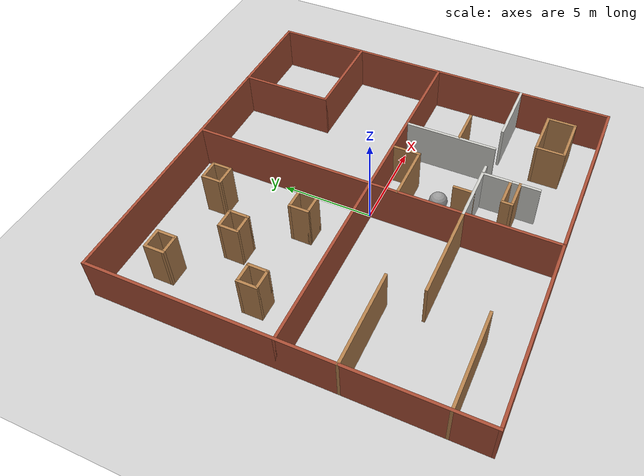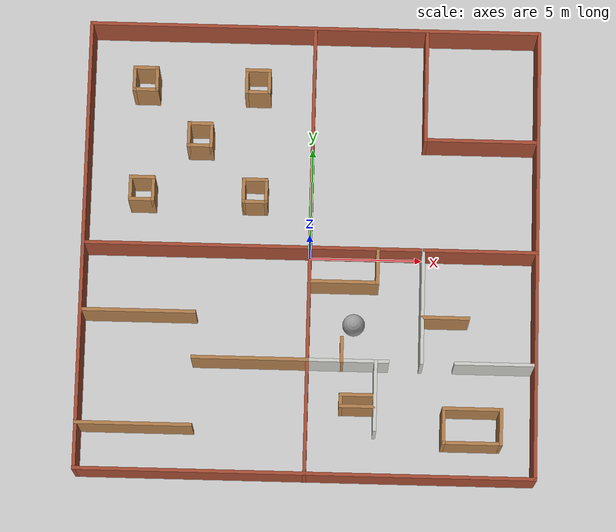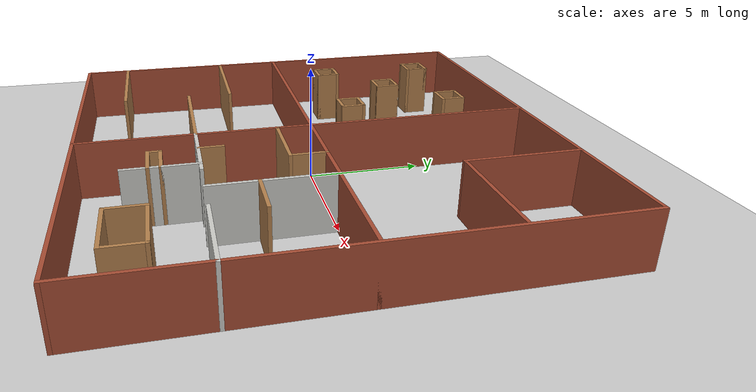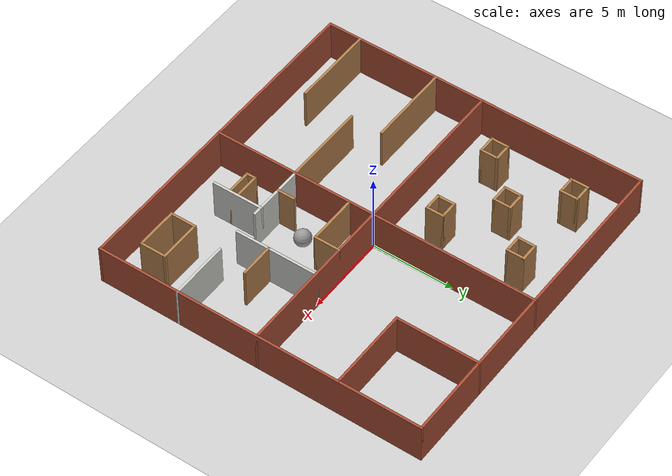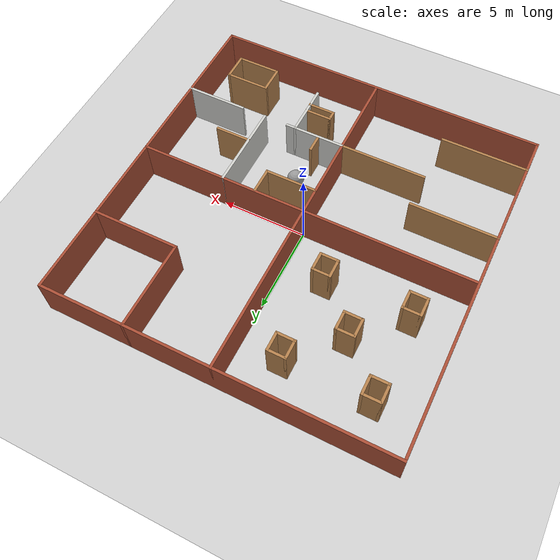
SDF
<sdf version="1.7">
 <world name="default">
  <light name="sun" type="directional">
   <pose>0 0 10 0 -0 0</pose>
   <diffuse>0.8 0.8 0.8 1</diffuse>
   <specular>0.2 0.2 0.2 1</specular>
   <attenuation>
    <range>1000</range>
    <constant>0.9</constant>
    <linear>0.01</linear>
    <quadratic>0.001</quadratic>
   </attenuation>
   <direction>-0.5 0.1 -0.9</direction>
   <spot><inner_angle>0</inner_angle><outer_angle>0</outer_angle><falloff>0</falloff></spot>
  </light>
  <model name="ground_plane">
   <static>1</static>
   <link name="link">
    <collision name="collision">
     <geometry><plane><normal>0 0 1</normal><size>100 100</size></plane></geometry>
     <surface>
      <contact><collide_bitmask>65535</collide_bitmask></contact>
      <friction><ode><mu>100</mu><mu2>50</mu2></ode></friction>
     </surface>
    </collision>
    <visual name="visual">
     <cast_shadows>0</cast_shadows>
     <geometry><plane><normal>0 0 1</normal><size>100 100</size></plane></geometry>
     <material>
      <script><uri>file://media/materials/scripts/gazebo.material</uri><name>Gazebo/Grey</name></script>
     </material>
    </visual>
   </link>
  </model>
  <gravity>0 0 -9.8</gravity>
  <magnetic_field>6e-06 2.3e-05 -4.2e-05</magnetic_field>
  <atmosphere type="adiabatic"/>
  <physics type="ode">
   <max_step_size>0.001</max_step_size>
   <real_time_factor>1</real_time_factor>
   <real_time_update_rate>1000</real_time_update_rate>
  </physics>
  <scene><ambient>0.4 0.4 0.4 1</ambient><background>0.7 0.7 0.7 1</background><shadows>1</shadows></scene>
  <spherical_coordinates>
   <surface_model>EARTH_WGS84</surface_model>
   <latitude_deg>0</latitude_deg>
   <longitude_deg>0</longitude_deg>
   <elevation>0</elevation>
   <heading_deg>0</heading_deg>
  </spherical_coordinates>
  <model name="Room_Curriculum">
   <link name="Wall_0">
    <pose>0 10 0 0 -0 0</pose>
    <visual name="Wall_0_Visual">
     <pose>0 0 1.25 0 -0 0</pose>
     <geometry><box><size>20.15 0.15 2.5</size></box></geometry>
     <material>
      <script><uri>file://media/materials/scripts/gazebo.material</uri><name>Gazebo/Bricks</name></script>
      <ambient>1 1 1 1</ambient>
      <shader type="pixel"/>
     </material>
     <meta><layer>0</layer></meta>
    </visual>
    <collision name="Wall_0_Collision">
     <pose>0 0 1.25 0 -0 0</pose>
     <geometry><box><size>20.15 0.15 2.5</size></box></geometry>
     <surface>
      <friction>
       <ode><mu>1</mu><mu2>1</mu2><fdir1>0 0 0</fdir1><slip1>0</slip1><slip2>0</slip2></ode>
       <torsional>
        <coefficient>1</coefficient>
        <patch_radius>0</patch_radius>
        <surface_radius>0</surface_radius>
        <use_patch_radius>1</use_patch_radius>
        <ode><slip>0</slip></ode>
       </torsional>
      </friction>
      <bounce><restitution_coefficient>0</restitution_coefficient><threshold>1e+06</threshold></bounce>
      <contact>
       <collide_without_contact>0</collide_without_contact>
       <collide_without_contact_bitmask>1</collide_without_contact_bitmask>
       <collide_bitmask>1</collide_bitmask>
       <ode>
        <soft_cfm>0</soft_cfm>
        <soft_erp>0.2</soft_erp>
        <kp>1e+13</kp>
        <kd>1</kd>
        <max_vel>0.01</max_vel>
        <min_depth>0</min_depth>
       </ode>
       <bullet>
        <split_impulse>1</split_impulse>
        <split_impulse_penetration_threshold>-0.01</split_impulse_penetration_threshold>
        <soft_cfm>0</soft_cfm>
        <soft_erp>0.2</soft_erp>
        <kp>1e+13</kp>
        <kd>1</kd>
       </bullet>
      </contact>
     </surface>
    </collision>
   </link>
   <link name="Wall_1">
    <pose>10 0 0 0 0 -1.5708</pose>
    <visual name="Wall_1_Visual">
     <pose>0 0 1.25 0 -0 0</pose>
     <geometry><box><size>20.15 0.15 2.5</size></box></geometry>
     <material>
      <script><uri>file://media/materials/scripts/gazebo.material</uri><name>Gazebo/Bricks</name></script>
      <ambient>1 1 1 1</ambient>
      <shader type="pixel"/>
     </material>
     <meta><layer>0</layer></meta>
    </visual>
    <collision name="Wall_1_Collision">
     <pose>0 0 1.25 0 -0 0</pose>
     <geometry><box><size>20.15 0.15 2.5</size></box></geometry>
     <surface>
      <friction>
       <ode><mu>1</mu><mu2>1</mu2><fdir1>0 0 0</fdir1><slip1>0</slip1><slip2>0</slip2></ode>
       <torsional>
        <coefficient>1</coefficient>
        <patch_radius>0</patch_radius>
        <surface_radius>0</surface_radius>
        <use_patch_radius>1</use_patch_radius>
        <ode><slip>0</slip></ode>
       </torsional>
      </friction>
      <bounce><restitution_coefficient>0</restitution_coefficient><threshold>1e+06</threshold></bounce>
      <contact>
       <collide_without_contact>0</collide_without_contact>
       <collide_without_contact_bitmask>1</collide_without_contact_bitmask>
       <collide_bitmask>1</collide_bitmask>
       <ode>
        <soft_cfm>0</soft_cfm>
        <soft_erp>0.2</soft_erp>
        <kp>1e+13</kp>
        <kd>1</kd>
        <max_vel>0.01</max_vel>
        <min_depth>0</min_depth>
       </ode>
       <bullet>
        <split_impulse>1</split_impulse>
        <split_impulse_penetration_threshold>-0.01</split_impulse_penetration_threshold>
        <soft_cfm>0</soft_cfm>
        <soft_erp>0.2</soft_erp>
        <kp>1e+13</kp>
        <kd>1</kd>
       </bullet>
      </contact>
     </surface>
    </collision>
   </link>
   <link name="Wall_15">
    <pose>5 7.5 0 0 0 -1.5708</pose>
    <visual name="Wall_15_Visual">
     <pose>0 0 1.25 0 -0 0</pose>
     <geometry><box><size>5.15 0.15 2.5</size></box></geometry>
     <material>
      <script><uri>file://media/materials/scripts/gazebo.material</uri><name>Gazebo/Bricks</name></script>
      <ambient>1 1 1 1</ambient>
      <shader type="pixel"/>
     </material>
     <meta><layer>0</layer></meta>
    </visual>
    <collision name="Wall_15_Collision">
     <pose>0 0 1.25 0 -0 0</pose>
     <geometry><box><size>5.15 0.15 2.5</size></box></geometry>
     <surface>
      <friction>
       <ode><mu>1</mu><mu2>1</mu2><fdir1>0 0 0</fdir1><slip1>0</slip1><slip2>0</slip2></ode>
       <torsional>
        <coefficient>1</coefficient>
        <patch_radius>0</patch_radius>
        <surface_radius>0</surface_radius>
        <use_patch_radius>1</use_patch_radius>
        <ode><slip>0</slip></ode>
       </torsional>
      </friction>
      <bounce><restitution_coefficient>0</restitution_coefficient><threshold>1e+06</threshold></bounce>
      <contact>
       <collide_without_contact>0</collide_without_contact>
       <collide_without_contact_bitmask>1</collide_without_contact_bitmask>
       <collide_bitmask>1</collide_bitmask>
       <ode>
        <soft_cfm>0</soft_cfm>
        <soft_erp>0.2</soft_erp>
        <kp>1e+13</kp>
        <kd>1</kd>
        <max_vel>0.01</max_vel>
        <min_depth>0</min_depth>
       </ode>
       <bullet>
        <split_impulse>1</split_impulse>
        <split_impulse_penetration_threshold>-0.01</split_impulse_penetration_threshold>
        <soft_cfm>0</soft_cfm>
        <soft_erp>0.2</soft_erp>
        <kp>1e+13</kp>
        <kd>1</kd>
       </bullet>
      </contact>
     </surface>
    </collision>
   </link>
   <link name="Wall_16">
    <pose>7.5 5 0 0 -0 0</pose>
    <visual name="Wall_16_Visual">
     <pose>0 0 1.25 0 -0 0</pose>
     <geometry><box><size>5.15 0.15 2.5</size></box></geometry>
     <material>
      <script><uri>file://media/materials/scripts/gazebo.material</uri><name>Gazebo/Bricks</name></script>
      <ambient>1 1 1 1</ambient>
      <shader type="pixel"/>
     </material>
     <meta><layer>0</layer></meta>
    </visual>
    <collision name="Wall_16_Collision">
     <pose>0 0 1.25 0 -0 0</pose>
     <geometry><box><size>5.15 0.15 2.5</size></box></geometry>
     <surface>
      <friction>
       <ode><mu>1</mu><mu2>1</mu2><fdir1>0 0 0</fdir1><slip1>0</slip1><slip2>0</slip2></ode>
       <torsional>
        <coefficient>1</coefficient>
        <patch_radius>0</patch_radius>
        <surface_radius>0</surface_radius>
        <use_patch_radius>1</use_patch_radius>
        <ode><slip>0</slip></ode>
       </torsional>
      </friction>
      <bounce><restitution_coefficient>0</restitution_coefficient><threshold>1e+06</threshold></bounce>
      <contact>
       <collide_without_contact>0</collide_without_contact>
       <collide_without_contact_bitmask>1</collide_without_contact_bitmask>
       <collide_bitmask>1</collide_bitmask>
       <ode>
        <soft_cfm>0</soft_cfm>
        <soft_erp>0.2</soft_erp>
        <kp>1e+13</kp>
        <kd>1</kd>
        <max_vel>0.01</max_vel>
        <min_depth>0</min_depth>
       </ode>
       <bullet>
        <split_impulse>1</split_impulse>
        <split_impulse_penetration_threshold>-0.01</split_impulse_penetration_threshold>
        <soft_cfm>0</soft_cfm>
        <soft_erp>0.2</soft_erp>
        <kp>1e+13</kp>
        <kd>1</kd>
       </bullet>
      </contact>
     </surface>
    </collision>
   </link>
   <link name="Wall_18">
    <pose>-7.5 8 0 0 -0 0</pose>
    <visual name="Wall_18_Visual">
     <pose>0 0 1.25 0 -0 0</pose>
     <geometry><box><size>1.15 0.15 2.5</size></box></geometry>
     <material>
      <script><uri>file://media/materials/scripts/gazebo.material</uri><name>Gazebo/Wood</name></script>
      <ambient>1 1 1 1</ambient>
      <shader type="pixel"/>
     </material>
     <meta><layer>0</layer></meta>
    </visual>
    <collision name="Wall_18_Collision">
     <pose>0 0 1.25 0 -0 0</pose>
     <geometry><box><size>1.15 0.15 2.5</size></box></geometry>
     <surface>
      <friction>
       <ode><mu>1</mu><mu2>1</mu2><fdir1>0 0 0</fdir1><slip1>0</slip1><slip2>0</slip2></ode>
       <torsional>
        <coefficient>1</coefficient>
        <patch_radius>0</patch_radius>
        <surface_radius>0</surface_radius>
        <use_patch_radius>1</use_patch_radius>
        <ode><slip>0</slip></ode>
       </torsional>
      </friction>
      <bounce><restitution_coefficient>0</restitution_coefficient><threshold>1e+06</threshold></bounce>
      <contact>
       <collide_without_contact>0</collide_without_contact>
       <collide_without_contact_bitmask>1</collide_without_contact_bitmask>
       <collide_bitmask>1</collide_bitmask>
       <ode>
        <soft_cfm>0</soft_cfm>
        <soft_erp>0.2</soft_erp>
        <kp>1e+13</kp>
        <kd>1</kd>
        <max_vel>0.01</max_vel>
        <min_depth>0</min_depth>
       </ode>
       <bullet>
        <split_impulse>1</split_impulse>
        <split_impulse_penetration_threshold>-0.01</split_impulse_penetration_threshold>
        <soft_cfm>0</soft_cfm>
        <soft_erp>0.2</soft_erp>
        <kp>1e+13</kp>
        <kd>1</kd>
       </bullet>
      </contact>
     </surface>
    </collision>
   </link>
   <link name="Wall_19">
    <pose>-7 7.5 0 0 0 -1.5708</pose>
    <visual name="Wall_19_Visual">
     <pose>0 0 1.25 0 -0 0</pose>
     <geometry><box><size>1.15 0.15 2.5</size></box></geometry>
     <material>
      <script><uri>file://media/materials/scripts/gazebo.material</uri><name>Gazebo/Wood</name></script>
      <ambient>1 1 1 1</ambient>
      <shader type="pixel"/>
     </material>
     <meta><layer>0</layer></meta>
    </visual>
    <collision name="Wall_19_Collision">
     <pose>0 0 1.25 0 -0 0</pose>
     <geometry><box><size>1.15 0.15 2.5</size></box></geometry>
     <surface>
      <friction>
       <ode><mu>1</mu><mu2>1</mu2><fdir1>0 0 0</fdir1><slip1>0</slip1><slip2>0</slip2></ode>
       <torsional>
        <coefficient>1</coefficient>
        <patch_radius>0</patch_radius>
        <surface_radius>0</surface_radius>
        <use_patch_radius>1</use_patch_radius>
        <ode><slip>0</slip></ode>
       </torsional>
      </friction>
      <bounce><restitution_coefficient>0</restitution_coefficient><threshold>1e+06</threshold></bounce>
      <contact>
       <collide_without_contact>0</collide_without_contact>
       <collide_without_contact_bitmask>1</collide_without_contact_bitmask>
       <collide_bitmask>1</collide_bitmask>
       <ode>
        <soft_cfm>0</soft_cfm>
        <soft_erp>0.2</soft_erp>
        <kp>1e+13</kp>
        <kd>1</kd>
        <max_vel>0.01</max_vel>
        <min_depth>0</min_depth>
       </ode>
       <bullet>
        <split_impulse>1</split_impulse>
        <split_impulse_penetration_threshold>-0.01</split_impulse_penetration_threshold>
        <soft_cfm>0</soft_cfm>
        <soft_erp>0.2</soft_erp>
        <kp>1e+13</kp>
        <kd>1</kd>
       </bullet>
      </contact>
     </surface>
    </collision>
   </link>
   <link name="Wall_2">
    <pose>0 -10 0 0 -0 3.14159</pose>
    <visual name="Wall_2_Visual">
     <pose>0 0 1.25 0 -0 0</pose>
     <geometry><box><size>20.15 0.15 2.5</size></box></geometry>
     <material>
      <script><uri>file://media/materials/scripts/gazebo.material</uri><name>Gazebo/Bricks</name></script>
      <ambient>1 1 1 1</ambient>
      <shader type="pixel"/>
     </material>
     <meta><layer>0</layer></meta>
    </visual>
    <collision name="Wall_2_Collision">
     <pose>0 0 1.25 0 -0 0</pose>
     <geometry><box><size>20.15 0.15 2.5</size></box></geometry>
     <surface>
      <friction>
       <ode><mu>1</mu><mu2>1</mu2><fdir1>0 0 0</fdir1><slip1>0</slip1><slip2>0</slip2></ode>
       <torsional>
        <coefficient>1</coefficient>
        <patch_radius>0</patch_radius>
        <surface_radius>0</surface_radius>
        <use_patch_radius>1</use_patch_radius>
        <ode><slip>0</slip></ode>
       </torsional>
      </friction>
      <bounce><restitution_coefficient>0</restitution_coefficient><threshold>1e+06</threshold></bounce>
      <contact>
       <collide_without_contact>0</collide_without_contact>
       <collide_without_contact_bitmask>1</collide_without_contact_bitmask>
       <collide_bitmask>1</collide_bitmask>
       <ode>
        <soft_cfm>0</soft_cfm>
        <soft_erp>0.2</soft_erp>
        <kp>1e+13</kp>
        <kd>1</kd>
        <max_vel>0.01</max_vel>
        <min_depth>0</min_depth>
       </ode>
       <bullet>
        <split_impulse>1</split_impulse>
        <split_impulse_penetration_threshold>-0.01</split_impulse_penetration_threshold>
        <soft_cfm>0</soft_cfm>
        <soft_erp>0.2</soft_erp>
        <kp>1e+13</kp>
        <kd>1</kd>
       </bullet>
      </contact>
     </surface>
    </collision>
   </link>
   <link name="Wall_20">
    <pose>-7.5 7 0 0 -0 3.14159</pose>
    <visual name="Wall_20_Visual">
     <pose>0 0 1.25 0 -0 0</pose>
     <geometry><box><size>1.15 0.15 2.5</size></box></geometry>
     <material>
      <script><uri>file://media/materials/scripts/gazebo.material</uri><name>Gazebo/Wood</name></script>
      <ambient>1 1 1 1</ambient>
      <shader type="pixel"/>
     </material>
     <meta><layer>0</layer></meta>
    </visual>
    <collision name="Wall_20_Collision">
     <pose>0 0 1.25 0 -0 0</pose>
     <geometry><box><size>1.15 0.15 2.5</size></box></geometry>
     <surface>
      <friction>
       <ode><mu>1</mu><mu2>1</mu2><fdir1>0 0 0</fdir1><slip1>0</slip1><slip2>0</slip2></ode>
       <torsional>
        <coefficient>1</coefficient>
        <patch_radius>0</patch_radius>
        <surface_radius>0</surface_radius>
        <use_patch_radius>1</use_patch_radius>
        <ode><slip>0</slip></ode>
       </torsional>
      </friction>
      <bounce><restitution_coefficient>0</restitution_coefficient><threshold>1e+06</threshold></bounce>
      <contact>
       <collide_without_contact>0</collide_without_contact>
       <collide_without_contact_bitmask>1</collide_without_contact_bitmask>
       <collide_bitmask>1</collide_bitmask>
       <ode>
        <soft_cfm>0</soft_cfm>
        <soft_erp>0.2</soft_erp>
        <kp>1e+13</kp>
        <kd>1</kd>
        <max_vel>0.01</max_vel>
        <min_depth>0</min_depth>
       </ode>
       <bullet>
        <split_impulse>1</split_impulse>
        <split_impulse_penetration_threshold>-0.01</split_impulse_penetration_threshold>
        <soft_cfm>0</soft_cfm>
        <soft_erp>0.2</soft_erp>
        <kp>1e+13</kp>
        <kd>1</kd>
       </bullet>
      </contact>
     </surface>
    </collision>
   </link>
   <link name="Wall_21">
    <pose>-8 7.5 0 0 -0 1.5708</pose>
    <visual name="Wall_21_Visual">
     <pose>0 0 1.25 0 -0 0</pose>
     <geometry><box><size>1.15 0.15 2.5</size></box></geometry>
     <material>
      <script><uri>file://media/materials/scripts/gazebo.material</uri><name>Gazebo/Wood</name></script>
      <ambient>1 1 1 1</ambient>
      <shader type="pixel"/>
     </material>
     <meta><layer>0</layer></meta>
    </visual>
    <collision name="Wall_21_Collision">
     <pose>0 0 1.25 0 -0 0</pose>
     <geometry><box><size>1.15 0.15 2.5</size></box></geometry>
     <surface>
      <friction>
       <ode><mu>1</mu><mu2>1</mu2><fdir1>0 0 0</fdir1><slip1>0</slip1><slip2>0</slip2></ode>
       <torsional>
        <coefficient>1</coefficient>
        <patch_radius>0</patch_radius>
        <surface_radius>0</surface_radius>
        <use_patch_radius>1</use_patch_radius>
        <ode><slip>0</slip></ode>
       </torsional>
      </friction>
      <bounce><restitution_coefficient>0</restitution_coefficient><threshold>1e+06</threshold></bounce>
      <contact>
       <collide_without_contact>0</collide_without_contact>
       <collide_without_contact_bitmask>1</collide_without_contact_bitmask>
       <collide_bitmask>1</collide_bitmask>
       <ode>
        <soft_cfm>0</soft_cfm>
        <soft_erp>0.2</soft_erp>
        <kp>1e+13</kp>
        <kd>1</kd>
        <max_vel>0.01</max_vel>
        <min_depth>0</min_depth>
       </ode>
       <bullet>
        <split_impulse>1</split_impulse>
        <split_impulse_penetration_threshold>-0.01</split_impulse_penetration_threshold>
        <soft_cfm>0</soft_cfm>
        <soft_erp>0.2</soft_erp>
        <kp>1e+13</kp>
        <kd>1</kd>
       </bullet>
      </contact>
     </surface>
    </collision>
   </link>
   <link name="Wall_23">
    <pose>-5.5 5 0 0 0 -1.5708</pose>
    <visual name="Wall_23_Visual">
     <pose>0 0 1.25 0 -0 0</pose>
     <geometry><box><size>1.15 0.15 2.5</size></box></geometry>
     <material>
      <script><uri>file://media/materials/scripts/gazebo.material</uri><name>Gazebo/Wood</name></script>
      <ambient>1 1 1 1</ambient>
      <shader type="pixel"/>
     </material>
     <meta><layer>0</layer></meta>
    </visual>
    <collision name="Wall_23_Collision">
     <pose>0 0 1.25 0 -0 0</pose>
     <geometry><box><size>1.15 0.15 2.5</size></box></geometry>
     <surface>
      <friction>
       <ode><mu>1</mu><mu2>1</mu2><fdir1>0 0 0</fdir1><slip1>0</slip1><slip2>0</slip2></ode>
       <torsional>
        <coefficient>1</coefficient>
        <patch_radius>0</patch_radius>
        <surface_radius>0</surface_radius>
        <use_patch_radius>1</use_patch_radius>
        <ode><slip>0</slip></ode>
       </torsional>
      </friction>
      <bounce><restitution_coefficient>0</restitution_coefficient><threshold>1e+06</threshold></bounce>
      <contact>
       <collide_without_contact>0</collide_without_contact>
       <collide_without_contact_bitmask>1</collide_without_contact_bitmask>
       <collide_bitmask>1</collide_bitmask>
       <ode>
        <soft_cfm>0</soft_cfm>
        <soft_erp>0.2</soft_erp>
        <kp>1e+13</kp>
        <kd>1</kd>
        <max_vel>0.01</max_vel>
        <min_depth>0</min_depth>
       </ode>
       <bullet>
        <split_impulse>1</split_impulse>
        <split_impulse_penetration_threshold>-0.01</split_impulse_penetration_threshold>
        <soft_cfm>0</soft_cfm>
        <soft_erp>0.2</soft_erp>
        <kp>1e+13</kp>
        <kd>1</kd>
       </bullet>
      </contact>
     </surface>
    </collision>
   </link>
   <link name="Wall_24">
    <pose>-5 4.5 0 0 -0 0</pose>
    <visual name="Wall_24_Visual">
     <pose>0 0 1.25 0 -0 0</pose>
     <geometry><box><size>1.15 0.15 2.5</size></box></geometry>
     <material>
      <script><uri>file://media/materials/scripts/gazebo.material</uri><name>Gazebo/Wood</name></script>
      <ambient>1 1 1 1</ambient>
      <shader type="pixel"/>
     </material>
     <meta><layer>0</layer></meta>
    </visual>
    <collision name="Wall_24_Collision">
     <pose>0 0 1.25 0 -0 0</pose>
     <geometry><box><size>1.15 0.15 2.5</size></box></geometry>
     <surface>
      <friction>
       <ode><mu>1</mu><mu2>1</mu2><fdir1>0 0 0</fdir1><slip1>0</slip1><slip2>0</slip2></ode>
       <torsional>
        <coefficient>1</coefficient>
        <patch_radius>0</patch_radius>
        <surface_radius>0</surface_radius>
        <use_patch_radius>1</use_patch_radius>
        <ode><slip>0</slip></ode>
       </torsional>
      </friction>
      <bounce><restitution_coefficient>0</restitution_coefficient><threshold>1e+06</threshold></bounce>
      <contact>
       <collide_without_contact>0</collide_without_contact>
       <collide_without_contact_bitmask>1</collide_without_contact_bitmask>
       <collide_bitmask>1</collide_bitmask>
       <ode>
        <soft_cfm>0</soft_cfm>
        <soft_erp>0.2</soft_erp>
        <kp>1e+13</kp>
        <kd>1</kd>
        <max_vel>0.01</max_vel>
        <min_depth>0</min_depth>
       </ode>
       <bullet>
        <split_impulse>1</split_impulse>
        <split_impulse_penetration_threshold>-0.01</split_impulse_penetration_threshold>
        <soft_cfm>0</soft_cfm>
        <soft_erp>0.2</soft_erp>
        <kp>1e+13</kp>
        <kd>1</kd>
       </bullet>
      </contact>
     </surface>
    </collision>
   </link>
   <link name="Wall_25">
    <pose>-4.5 5 0 0 -0 1.5708</pose>
    <visual name="Wall_25_Visual">
     <pose>0 0 1.25 0 -0 0</pose>
     <geometry><box><size>1.15 0.15 2.5</size></box></geometry>
     <material>
      <script><uri>file://media/materials/scripts/gazebo.material</uri><name>Gazebo/Wood</name></script>
      <ambient>1 1 1 1</ambient>
      <shader type="pixel"/>
     </material>
     <meta><layer>0</layer></meta>
    </visual>
    <collision name="Wall_25_Collision">
     <pose>0 0 1.25 0 -0 0</pose>
     <geometry><box><size>1.15 0.15 2.5</size></box></geometry>
     <surface>
      <friction>
       <ode><mu>1</mu><mu2>1</mu2><fdir1>0 0 0</fdir1><slip1>0</slip1><slip2>0</slip2></ode>
       <torsional>
        <coefficient>1</coefficient>
        <patch_radius>0</patch_radius>
        <surface_radius>0</surface_radius>
        <use_patch_radius>1</use_patch_radius>
        <ode><slip>0</slip></ode>
       </torsional>
      </friction>
      <bounce><restitution_coefficient>0</restitution_coefficient><threshold>1e+06</threshold></bounce>
      <contact>
       <collide_without_contact>0</collide_without_contact>
       <collide_without_contact_bitmask>1</collide_without_contact_bitmask>
       <collide_bitmask>1</collide_bitmask>
       <ode>
        <soft_cfm>0</soft_cfm>
        <soft_erp>0.2</soft_erp>
        <kp>1e+13</kp>
        <kd>1</kd>
        <max_vel>0.01</max_vel>
        <min_depth>0</min_depth>
       </ode>
       <bullet>
        <split_impulse>1</split_impulse>
        <split_impulse_penetration_threshold>-0.01</split_impulse_penetration_threshold>
        <soft_cfm>0</soft_cfm>
        <soft_erp>0.2</soft_erp>
        <kp>1e+13</kp>
        <kd>1</kd>
       </bullet>
      </contact>
     </surface>
    </collision>
   </link>
   <link name="Wall_26">
    <pose>-5 5.5 0 0 -0 3.14159</pose>
    <visual name="Wall_26_Visual">
     <pose>0 0 1.25 0 -0 0</pose>
     <geometry><box><size>1.15 0.15 2.5</size></box></geometry>
     <material>
      <script><uri>file://media/materials/scripts/gazebo.material</uri><name>Gazebo/Wood</name></script>
      <ambient>1 1 1 1</ambient>
      <shader type="pixel"/>
     </material>
     <meta><layer>0</layer></meta>
    </visual>
    <collision name="Wall_26_Collision">
     <pose>0 0 1.25 0 -0 0</pose>
     <geometry><box><size>1.15 0.15 2.5</size></box></geometry>
     <surface>
      <friction>
       <ode><mu>1</mu><mu2>1</mu2><fdir1>0 0 0</fdir1><slip1>0</slip1><slip2>0</slip2></ode>
       <torsional>
        <coefficient>1</coefficient>
        <patch_radius>0</patch_radius>
        <surface_radius>0</surface_radius>
        <use_patch_radius>1</use_patch_radius>
        <ode><slip>0</slip></ode>
       </torsional>
      </friction>
      <bounce><restitution_coefficient>0</restitution_coefficient><threshold>1e+06</threshold></bounce>
      <contact>
       <collide_without_contact>0</collide_without_contact>
       <collide_without_contact_bitmask>1</collide_without_contact_bitmask>
       <collide_bitmask>1</collide_bitmask>
       <ode>
        <soft_cfm>0</soft_cfm>
        <soft_erp>0.2</soft_erp>
        <kp>1e+13</kp>
        <kd>1</kd>
        <max_vel>0.01</max_vel>
        <min_depth>0</min_depth>
       </ode>
       <bullet>
        <split_impulse>1</split_impulse>
        <split_impulse_penetration_threshold>-0.01</split_impulse_penetration_threshold>
        <soft_cfm>0</soft_cfm>
        <soft_erp>0.2</soft_erp>
        <kp>1e+13</kp>
        <kd>1</kd>
       </bullet>
      </contact>
     </surface>
    </collision>
   </link>
   <link name="Wall_28">
    <pose>-2.5 8 0 0 -0 0</pose>
    <visual name="Wall_28_Visual">
     <pose>0 0 1.25 0 -0 0</pose>
     <geometry><box><size>1.15 0.15 2.5</size></box></geometry>
     <material>
      <script><uri>file://media/materials/scripts/gazebo.material</uri><name>Gazebo/Wood</name></script>
      <ambient>1 1 1 1</ambient>
      <shader type="pixel"/>
     </material>
     <meta><layer>0</layer></meta>
    </visual>
    <collision name="Wall_28_Collision">
     <pose>0 0 1.25 0 -0 0</pose>
     <geometry><box><size>1.15 0.15 2.5</size></box></geometry>
     <surface>
      <friction>
       <ode><mu>1</mu><mu2>1</mu2><fdir1>0 0 0</fdir1><slip1>0</slip1><slip2>0</slip2></ode>
       <torsional>
        <coefficient>1</coefficient>
        <patch_radius>0</patch_radius>
        <surface_radius>0</surface_radius>
        <use_patch_radius>1</use_patch_radius>
        <ode><slip>0</slip></ode>
       </torsional>
      </friction>
      <bounce><restitution_coefficient>0</restitution_coefficient><threshold>1e+06</threshold></bounce>
      <contact>
       <collide_without_contact>0</collide_without_contact>
       <collide_without_contact_bitmask>1</collide_without_contact_bitmask>
       <collide_bitmask>1</collide_bitmask>
       <ode>
        <soft_cfm>0</soft_cfm>
        <soft_erp>0.2</soft_erp>
        <kp>1e+13</kp>
        <kd>1</kd>
        <max_vel>0.01</max_vel>
        <min_depth>0</min_depth>
       </ode>
       <bullet>
        <split_impulse>1</split_impulse>
        <split_impulse_penetration_threshold>-0.01</split_impulse_penetration_threshold>
        <soft_cfm>0</soft_cfm>
        <soft_erp>0.2</soft_erp>
        <kp>1e+13</kp>
        <kd>1</kd>
       </bullet>
      </contact>
     </surface>
    </collision>
   </link>
   <link name="Wall_29">
    <pose>-2 7.5 0 0 0 -1.5708</pose>
    <visual name="Wall_29_Visual">
     <pose>0 0 1.25 0 -0 0</pose>
     <geometry><box><size>1.15 0.15 2.5</size></box></geometry>
     <material>
      <script><uri>file://media/materials/scripts/gazebo.material</uri><name>Gazebo/Wood</name></script>
      <ambient>1 1 1 1</ambient>
      <shader type="pixel"/>
     </material>
     <meta><layer>0</layer></meta>
    </visual>
    <collision name="Wall_29_Collision">
     <pose>0 0 1.25 0 -0 0</pose>
     <geometry><box><size>1.15 0.15 2.5</size></box></geometry>
     <surface>
      <friction>
       <ode><mu>1</mu><mu2>1</mu2><fdir1>0 0 0</fdir1><slip1>0</slip1><slip2>0</slip2></ode>
       <torsional>
        <coefficient>1</coefficient>
        <patch_radius>0</patch_radius>
        <surface_radius>0</surface_radius>
        <use_patch_radius>1</use_patch_radius>
        <ode><slip>0</slip></ode>
       </torsional>
      </friction>
      <bounce><restitution_coefficient>0</restitution_coefficient><threshold>1e+06</threshold></bounce>
      <contact>
       <collide_without_contact>0</collide_without_contact>
       <collide_without_contact_bitmask>1</collide_without_contact_bitmask>
       <collide_bitmask>1</collide_bitmask>
       <ode>
        <soft_cfm>0</soft_cfm>
        <soft_erp>0.2</soft_erp>
        <kp>1e+13</kp>
        <kd>1</kd>
        <max_vel>0.01</max_vel>
        <min_depth>0</min_depth>
       </ode>
       <bullet>
        <split_impulse>1</split_impulse>
        <split_impulse_penetration_threshold>-0.01</split_impulse_penetration_threshold>
        <soft_cfm>0</soft_cfm>
        <soft_erp>0.2</soft_erp>
        <kp>1e+13</kp>
        <kd>1</kd>
       </bullet>
      </contact>
     </surface>
    </collision>
   </link>
   <link name="Wall_3">
    <pose>-10 0 0 0 -0 1.5708</pose>
    <visual name="Wall_3_Visual">
     <pose>0 0 1.25 0 -0 0</pose>
     <geometry><box><size>20.15 0.15 2.5</size></box></geometry>
     <material>
      <script><uri>file://media/materials/scripts/gazebo.material</uri><name>Gazebo/Bricks</name></script>
      <ambient>1 1 1 1</ambient>
      <shader type="pixel"/>
     </material>
     <meta><layer>0</layer></meta>
    </visual>
    <collision name="Wall_3_Collision">
     <pose>0 0 1.25 0 -0 0</pose>
     <geometry><box><size>20.15 0.15 2.5</size></box></geometry>
     <surface>
      <friction>
       <ode><mu>1</mu><mu2>1</mu2><fdir1>0 0 0</fdir1><slip1>0</slip1><slip2>0</slip2></ode>
       <torsional>
        <coefficient>1</coefficient>
        <patch_radius>0</patch_radius>
        <surface_radius>0</surface_radius>
        <use_patch_radius>1</use_patch_radius>
        <ode><slip>0</slip></ode>
       </torsional>
      </friction>
      <bounce><restitution_coefficient>0</restitution_coefficient><threshold>1e+06</threshold></bounce>
      <contact>
       <collide_without_contact>0</collide_without_contact>
       <collide_without_contact_bitmask>1</collide_without_contact_bitmask>
       <collide_bitmask>1</collide_bitmask>
       <ode>
        <soft_cfm>0</soft_cfm>
        <soft_erp>0.2</soft_erp>
        <kp>1e+13</kp>
        <kd>1</kd>
        <max_vel>0.01</max_vel>
        <min_depth>0</min_depth>
       </ode>
       <bullet>
        <split_impulse>1</split_impulse>
        <split_impulse_penetration_threshold>-0.01</split_impulse_penetration_threshold>
        <soft_cfm>0</soft_cfm>
        <soft_erp>0.2</soft_erp>
        <kp>1e+13</kp>
        <kd>1</kd>
       </bullet>
      </contact>
     </surface>
    </collision>
   </link>
   <link name="Wall_30">
    <pose>-2.5 7 0 0 -0 3.14159</pose>
    <visual name="Wall_30_Visual">
     <pose>0 0 1.25 0 -0 0</pose>
     <geometry><box><size>1.15 0.15 2.5</size></box></geometry>
     <material>
      <script><uri>file://media/materials/scripts/gazebo.material</uri><name>Gazebo/Wood</name></script>
      <ambient>1 1 1 1</ambient>
      <shader type="pixel"/>
     </material>
     <meta><layer>0</layer></meta>
    </visual>
    <collision name="Wall_30_Collision">
     <pose>0 0 1.25 0 -0 0</pose>
     <geometry><box><size>1.15 0.15 2.5</size></box></geometry>
     <surface>
      <friction>
       <ode><mu>1</mu><mu2>1</mu2><fdir1>0 0 0</fdir1><slip1>0</slip1><slip2>0</slip2></ode>
       <torsional>
        <coefficient>1</coefficient>
        <patch_radius>0</patch_radius>
        <surface_radius>0</surface_radius>
        <use_patch_radius>1</use_patch_radius>
        <ode><slip>0</slip></ode>
       </torsional>
      </friction>
      <bounce><restitution_coefficient>0</restitution_coefficient><threshold>1e+06</threshold></bounce>
      <contact>
       <collide_without_contact>0</collide_without_contact>
       <collide_without_contact_bitmask>1</collide_without_contact_bitmask>
       <collide_bitmask>1</collide_bitmask>
       <ode>
        <soft_cfm>0</soft_cfm>
        <soft_erp>0.2</soft_erp>
        <kp>1e+13</kp>
        <kd>1</kd>
        <max_vel>0.01</max_vel>
        <min_depth>0</min_depth>
       </ode>
       <bullet>
        <split_impulse>1</split_impulse>
        <split_impulse_penetration_threshold>-0.01</split_impulse_penetration_threshold>
        <soft_cfm>0</soft_cfm>
        <soft_erp>0.2</soft_erp>
        <kp>1e+13</kp>
        <kd>1</kd>
       </bullet>
      </contact>
     </surface>
    </collision>
   </link>
   <link name="Wall_31">
    <pose>-3 7.5 0 0 -0 1.5708</pose>
    <visual name="Wall_31_Visual">
     <pose>0 0 1.25 0 -0 0</pose>
     <geometry><box><size>1.15 0.15 2.5</size></box></geometry>
     <material>
      <script><uri>file://media/materials/scripts/gazebo.material</uri><name>Gazebo/Wood</name></script>
      <ambient>1 1 1 1</ambient>
      <shader type="pixel"/>
     </material>
     <meta><layer>0</layer></meta>
    </visual>
    <collision name="Wall_31_Collision">
     <pose>0 0 1.25 0 -0 0</pose>
     <geometry><box><size>1.15 0.15 2.5</size></box></geometry>
     <surface>
      <friction>
       <ode><mu>1</mu><mu2>1</mu2><fdir1>0 0 0</fdir1><slip1>0</slip1><slip2>0</slip2></ode>
       <torsional>
        <coefficient>1</coefficient>
        <patch_radius>0</patch_radius>
        <surface_radius>0</surface_radius>
        <use_patch_radius>1</use_patch_radius>
        <ode><slip>0</slip></ode>
       </torsional>
      </friction>
      <bounce><restitution_coefficient>0</restitution_coefficient><threshold>1e+06</threshold></bounce>
      <contact>
       <collide_without_contact>0</collide_without_contact>
       <collide_without_contact_bitmask>1</collide_without_contact_bitmask>
       <collide_bitmask>1</collide_bitmask>
       <ode>
        <soft_cfm>0</soft_cfm>
        <soft_erp>0.2</soft_erp>
        <kp>1e+13</kp>
        <kd>1</kd>
        <max_vel>0.01</max_vel>
        <min_depth>0</min_depth>
       </ode>
       <bullet>
        <split_impulse>1</split_impulse>
        <split_impulse_penetration_threshold>-0.01</split_impulse_penetration_threshold>
        <soft_cfm>0</soft_cfm>
        <soft_erp>0.2</soft_erp>
        <kp>1e+13</kp>
        <kd>1</kd>
       </bullet>
      </contact>
     </surface>
    </collision>
   </link>
   <link name="Wall_33">
    <pose>-8 2.5 0 0 0 -1.5708</pose>
    <visual name="Wall_33_Visual">
     <pose>0 0 1.25 0 -0 0</pose>
     <geometry><box><size>1.15 0.15 2.5</size></box></geometry>
     <material>
      <script><uri>file://media/materials/scripts/gazebo.material</uri><name>Gazebo/Wood</name></script>
      <ambient>1 1 1 1</ambient>
      <shader type="pixel"/>
     </material>
     <meta><layer>0</layer></meta>
    </visual>
    <collision name="Wall_33_Collision">
     <pose>0 0 1.25 0 -0 0</pose>
     <geometry><box><size>1.15 0.15 2.5</size></box></geometry>
     <surface>
      <friction>
       <ode><mu>1</mu><mu2>1</mu2><fdir1>0 0 0</fdir1><slip1>0</slip1><slip2>0</slip2></ode>
       <torsional>
        <coefficient>1</coefficient>
        <patch_radius>0</patch_radius>
        <surface_radius>0</surface_radius>
        <use_patch_radius>1</use_patch_radius>
        <ode><slip>0</slip></ode>
       </torsional>
      </friction>
      <bounce><restitution_coefficient>0</restitution_coefficient><threshold>1e+06</threshold></bounce>
      <contact>
       <collide_without_contact>0</collide_without_contact>
       <collide_without_contact_bitmask>1</collide_without_contact_bitmask>
       <collide_bitmask>1</collide_bitmask>
       <ode>
        <soft_cfm>0</soft_cfm>
        <soft_erp>0.2</soft_erp>
        <kp>1e+13</kp>
        <kd>1</kd>
        <max_vel>0.01</max_vel>
        <min_depth>0</min_depth>
       </ode>
       <bullet>
        <split_impulse>1</split_impulse>
        <split_impulse_penetration_threshold>-0.01</split_impulse_penetration_threshold>
        <soft_cfm>0</soft_cfm>
        <soft_erp>0.2</soft_erp>
        <kp>1e+13</kp>
        <kd>1</kd>
       </bullet>
      </contact>
     </surface>
    </collision>
   </link>
   <link name="Wall_34">
    <pose>-7.5 2 0 0 -0 0</pose>
    <visual name="Wall_34_Visual">
     <pose>0 0 1.25 0 -0 0</pose>
     <geometry><box><size>1.15 0.15 2.5</size></box></geometry>
     <material>
      <script><uri>file://media/materials/scripts/gazebo.material</uri><name>Gazebo/Wood</name></script>
      <ambient>1 1 1 1</ambient>
      <shader type="pixel"/>
     </material>
     <meta><layer>0</layer></meta>
    </visual>
    <collision name="Wall_34_Collision">
     <pose>0 0 1.25 0 -0 0</pose>
     <geometry><box><size>1.15 0.15 2.5</size></box></geometry>
     <surface>
      <friction>
       <ode><mu>1</mu><mu2>1</mu2><fdir1>0 0 0</fdir1><slip1>0</slip1><slip2>0</slip2></ode>
       <torsional>
        <coefficient>1</coefficient>
        <patch_radius>0</patch_radius>
        <surface_radius>0</surface_radius>
        <use_patch_radius>1</use_patch_radius>
        <ode><slip>0</slip></ode>
       </torsional>
      </friction>
      <bounce><restitution_coefficient>0</restitution_coefficient><threshold>1e+06</threshold></bounce>
      <contact>
       <collide_without_contact>0</collide_without_contact>
       <collide_without_contact_bitmask>1</collide_without_contact_bitmask>
       <collide_bitmask>1</collide_bitmask>
       <ode>
        <soft_cfm>0</soft_cfm>
        <soft_erp>0.2</soft_erp>
        <kp>1e+13</kp>
        <kd>1</kd>
        <max_vel>0.01</max_vel>
        <min_depth>0</min_depth>
       </ode>
       <bullet>
        <split_impulse>1</split_impulse>
        <split_impulse_penetration_threshold>-0.01</split_impulse_penetration_threshold>
        <soft_cfm>0</soft_cfm>
        <soft_erp>0.2</soft_erp>
        <kp>1e+13</kp>
        <kd>1</kd>
       </bullet>
      </contact>
     </surface>
    </collision>
   </link>
   <link name="Wall_35">
    <pose>-7 2.5 0 0 -0 1.5708</pose>
    <visual name="Wall_35_Visual">
     <pose>0 0 1.25 0 -0 0</pose>
     <geometry><box><size>1.15 0.15 2.5</size></box></geometry>
     <material>
      <script><uri>file://media/materials/scripts/gazebo.material</uri><name>Gazebo/Wood</name></script>
      <ambient>1 1 1 1</ambient>
      <shader type="pixel"/>
     </material>
     <meta><layer>0</layer></meta>
    </visual>
    <collision name="Wall_35_Collision">
     <pose>0 0 1.25 0 -0 0</pose>
     <geometry><box><size>1.15 0.15 2.5</size></box></geometry>
     <surface>
      <friction>
       <ode><mu>1</mu><mu2>1</mu2><fdir1>0 0 0</fdir1><slip1>0</slip1><slip2>0</slip2></ode>
       <torsional>
        <coefficient>1</coefficient>
        <patch_radius>0</patch_radius>
        <surface_radius>0</surface_radius>
        <use_patch_radius>1</use_patch_radius>
        <ode><slip>0</slip></ode>
       </torsional>
      </friction>
      <bounce><restitution_coefficient>0</restitution_coefficient><threshold>1e+06</threshold></bounce>
      <contact>
       <collide_without_contact>0</collide_without_contact>
       <collide_without_contact_bitmask>1</collide_without_contact_bitmask>
       <collide_bitmask>1</collide_bitmask>
       <ode>
        <soft_cfm>0</soft_cfm>
        <soft_erp>0.2</soft_erp>
        <kp>1e+13</kp>
        <kd>1</kd>
        <max_vel>0.01</max_vel>
        <min_depth>0</min_depth>
       </ode>
       <bullet>
        <split_impulse>1</split_impulse>
        <split_impulse_penetration_threshold>-0.01</split_impulse_penetration_threshold>
        <soft_cfm>0</soft_cfm>
        <soft_erp>0.2</soft_erp>
        <kp>1e+13</kp>
        <kd>1</kd>
       </bullet>
      </contact>
     </surface>
    </collision>
   </link>
   <link name="Wall_36">
    <pose>-7.5 3 0 0 -0 3.14159</pose>
    <visual name="Wall_36_Visual">
     <pose>0 0 1.25 0 -0 0</pose>
     <geometry><box><size>1.15 0.15 2.5</size></box></geometry>
     <material>
      <script><uri>file://media/materials/scripts/gazebo.material</uri><name>Gazebo/Wood</name></script>
      <ambient>1 1 1 1</ambient>
      <shader type="pixel"/>
     </material>
     <meta><layer>0</layer></meta>
    </visual>
    <collision name="Wall_36_Collision">
     <pose>0 0 1.25 0 -0 0</pose>
     <geometry><box><size>1.15 0.15 2.5</size></box></geometry>
     <surface>
      <friction>
       <ode><mu>1</mu><mu2>1</mu2><fdir1>0 0 0</fdir1><slip1>0</slip1><slip2>0</slip2></ode>
       <torsional>
        <coefficient>1</coefficient>
        <patch_radius>0</patch_radius>
        <surface_radius>0</surface_radius>
        <use_patch_radius>1</use_patch_radius>
        <ode><slip>0</slip></ode>
       </torsional>
      </friction>
      <bounce><restitution_coefficient>0</restitution_coefficient><threshold>1e+06</threshold></bounce>
      <contact>
       <collide_without_contact>0</collide_without_contact>
       <collide_without_contact_bitmask>1</collide_without_contact_bitmask>
       <collide_bitmask>1</collide_bitmask>
       <ode>
        <soft_cfm>0</soft_cfm>
        <soft_erp>0.2</soft_erp>
        <kp>1e+13</kp>
        <kd>1</kd>
        <max_vel>0.01</max_vel>
        <min_depth>0</min_depth>
       </ode>
       <bullet>
        <split_impulse>1</split_impulse>
        <split_impulse_penetration_threshold>-0.01</split_impulse_penetration_threshold>
        <soft_cfm>0</soft_cfm>
        <soft_erp>0.2</soft_erp>
        <kp>1e+13</kp>
        <kd>1</kd>
       </bullet>
      </contact>
     </surface>
    </collision>
   </link>
   <link name="Wall_38">
    <pose>-3 2.5 0 0 0 -1.5708</pose>
    <visual name="Wall_38_Visual">
     <pose>0 0 1.25 0 -0 0</pose>
     <geometry><box><size>1.15 0.15 2.5</size></box></geometry>
     <material>
      <script><uri>file://media/materials/scripts/gazebo.material</uri><name>Gazebo/Wood</name></script>
      <ambient>1 1 1 1</ambient>
      <shader type="pixel"/>
     </material>
     <meta><layer>0</layer></meta>
    </visual>
    <collision name="Wall_38_Collision">
     <pose>0 0 1.25 0 -0 0</pose>
     <geometry><box><size>1.15 0.15 2.5</size></box></geometry>
     <surface>
      <friction>
       <ode><mu>1</mu><mu2>1</mu2><fdir1>0 0 0</fdir1><slip1>0</slip1><slip2>0</slip2></ode>
       <torsional>
        <coefficient>1</coefficient>
        <patch_radius>0</patch_radius>
        <surface_radius>0</surface_radius>
        <use_patch_radius>1</use_patch_radius>
        <ode><slip>0</slip></ode>
       </torsional>
      </friction>
      <bounce><restitution_coefficient>0</restitution_coefficient><threshold>1e+06</threshold></bounce>
      <contact>
       <collide_without_contact>0</collide_without_contact>
       <collide_without_contact_bitmask>1</collide_without_contact_bitmask>
       <collide_bitmask>1</collide_bitmask>
       <ode>
        <soft_cfm>0</soft_cfm>
        <soft_erp>0.2</soft_erp>
        <kp>1e+13</kp>
        <kd>1</kd>
        <max_vel>0.01</max_vel>
        <min_depth>0</min_depth>
       </ode>
       <bullet>
        <split_impulse>1</split_impulse>
        <split_impulse_penetration_threshold>-0.01</split_impulse_penetration_threshold>
        <soft_cfm>0</soft_cfm>
        <soft_erp>0.2</soft_erp>
        <kp>1e+13</kp>
        <kd>1</kd>
       </bullet>
      </contact>
     </surface>
    </collision>
   </link>
   <link name="Wall_39">
    <pose>-2.5 2 0 0 -0 0</pose>
    <visual name="Wall_39_Visual">
     <pose>0 0 1.25 0 -0 0</pose>
     <geometry><box><size>1.15 0.15 2.5</size></box></geometry>
     <material>
      <script><uri>file://media/materials/scripts/gazebo.material</uri><name>Gazebo/Wood</name></script>
      <ambient>1 1 1 1</ambient>
      <shader type="pixel"/>
     </material>
     <meta><layer>0</layer></meta>
    </visual>
    <collision name="Wall_39_Collision">
     <pose>0 0 1.25 0 -0 0</pose>
     <geometry><box><size>1.15 0.15 2.5</size></box></geometry>
     <surface>
      <friction>
       <ode><mu>1</mu><mu2>1</mu2><fdir1>0 0 0</fdir1><slip1>0</slip1><slip2>0</slip2></ode>
       <torsional>
        <coefficient>1</coefficient>
        <patch_radius>0</patch_radius>
        <surface_radius>0</surface_radius>
        <use_patch_radius>1</use_patch_radius>
        <ode><slip>0</slip></ode>
       </torsional>
      </friction>
      <bounce><restitution_coefficient>0</restitution_coefficient><threshold>1e+06</threshold></bounce>
      <contact>
       <collide_without_contact>0</collide_without_contact>
       <collide_without_contact_bitmask>1</collide_without_contact_bitmask>
       <collide_bitmask>1</collide_bitmask>
       <ode>
        <soft_cfm>0</soft_cfm>
        <soft_erp>0.2</soft_erp>
        <kp>1e+13</kp>
        <kd>1</kd>
        <max_vel>0.01</max_vel>
        <min_depth>0</min_depth>
       </ode>
       <bullet>
        <split_impulse>1</split_impulse>
        <split_impulse_penetration_threshold>-0.01</split_impulse_penetration_threshold>
        <soft_cfm>0</soft_cfm>
        <soft_erp>0.2</soft_erp>
        <kp>1e+13</kp>
        <kd>1</kd>
       </bullet>
      </contact>
     </surface>
    </collision>
   </link>
   <link name="Wall_40">
    <pose>-2 2.5 0 0 -0 1.5708</pose>
    <visual name="Wall_40_Visual">
     <pose>0 0 1.25 0 -0 0</pose>
     <geometry><box><size>1.15 0.15 2.5</size></box></geometry>
     <material>
      <script><uri>file://media/materials/scripts/gazebo.material</uri><name>Gazebo/Wood</name></script>
      <ambient>1 1 1 1</ambient>
      <shader type="pixel"/>
     </material>
     <meta><layer>0</layer></meta>
    </visual>
    <collision name="Wall_40_Collision">
     <pose>0 0 1.25 0 -0 0</pose>
     <geometry><box><size>1.15 0.15 2.5</size></box></geometry>
     <surface>
      <friction>
       <ode><mu>1</mu><mu2>1</mu2><fdir1>0 0 0</fdir1><slip1>0</slip1><slip2>0</slip2></ode>
       <torsional>
        <coefficient>1</coefficient>
        <patch_radius>0</patch_radius>
        <surface_radius>0</surface_radius>
        <use_patch_radius>1</use_patch_radius>
        <ode><slip>0</slip></ode>
       </torsional>
      </friction>
      <bounce><restitution_coefficient>0</restitution_coefficient><threshold>1e+06</threshold></bounce>
      <contact>
       <collide_without_contact>0</collide_without_contact>
       <collide_without_contact_bitmask>1</collide_without_contact_bitmask>
       <collide_bitmask>1</collide_bitmask>
       <ode>
        <soft_cfm>0</soft_cfm>
        <soft_erp>0.2</soft_erp>
        <kp>1e+13</kp>
        <kd>1</kd>
        <max_vel>0.01</max_vel>
        <min_depth>0</min_depth>
       </ode>
       <bullet>
        <split_impulse>1</split_impulse>
        <split_impulse_penetration_threshold>-0.01</split_impulse_penetration_threshold>
        <soft_cfm>0</soft_cfm>
        <soft_erp>0.2</soft_erp>
        <kp>1e+13</kp>
        <kd>1</kd>
       </bullet>
      </contact>
     </surface>
    </collision>
   </link>
   <link name="Wall_41">
    <pose>-2.5 3 0 0 -0 3.14159</pose>
    <visual name="Wall_41_Visual">
     <pose>0 0 1.25 0 -0 0</pose>
     <geometry><box><size>1.15 0.15 2.5</size></box></geometry>
     <material>
      <script><uri>file://media/materials/scripts/gazebo.material</uri><name>Gazebo/Wood</name></script>
      <ambient>1 1 1 1</ambient>
      <shader type="pixel"/>
     </material>
     <meta><layer>0</layer></meta>
    </visual>
    <collision name="Wall_41_Collision">
     <pose>0 0 1.25 0 -0 0</pose>
     <geometry><box><size>1.15 0.15 2.5</size></box></geometry>
     <surface>
      <friction>
       <ode><mu>1</mu><mu2>1</mu2><fdir1>0 0 0</fdir1><slip1>0</slip1><slip2>0</slip2></ode>
       <torsional>
        <coefficient>1</coefficient>
        <patch_radius>0</patch_radius>
        <surface_radius>0</surface_radius>
        <use_patch_radius>1</use_patch_radius>
        <ode><slip>0</slip></ode>
       </torsional>
      </friction>
      <bounce><restitution_coefficient>0</restitution_coefficient><threshold>1e+06</threshold></bounce>
      <contact>
       <collide_without_contact>0</collide_without_contact>
       <collide_without_contact_bitmask>1</collide_without_contact_bitmask>
       <collide_bitmask>1</collide_bitmask>
       <ode>
        <soft_cfm>0</soft_cfm>
        <soft_erp>0.2</soft_erp>
        <kp>1e+13</kp>
        <kd>1</kd>
        <max_vel>0.01</max_vel>
        <min_depth>0</min_depth>
       </ode>
       <bullet>
        <split_impulse>1</split_impulse>
        <split_impulse_penetration_threshold>-0.01</split_impulse_penetration_threshold>
        <soft_cfm>0</soft_cfm>
        <soft_erp>0.2</soft_erp>
        <kp>1e+13</kp>
        <kd>1</kd>
       </bullet>
      </contact>
     </surface>
    </collision>
   </link>
   <link name="Wall_43">
    <pose>-7.5 -3 0 0 -0 0</pose>
    <visual name="Wall_43_Visual">
     <pose>0 0 1.25 0 -0 0</pose>
     <geometry><box><size>5.15 0.15 2.5</size></box></geometry>
     <material>
      <script><uri>file://media/materials/scripts/gazebo.material</uri><name>Gazebo/Wood</name></script>
      <ambient>1 1 1 1</ambient>
      <shader type="pixel"/>
     </material>
     <meta><layer>0</layer></meta>
    </visual>
    <collision name="Wall_43_Collision">
     <pose>0 0 1.25 0 -0 0</pose>
     <geometry><box><size>5.15 0.15 2.5</size></box></geometry>
     <surface>
      <friction>
       <ode><mu>1</mu><mu2>1</mu2><fdir1>0 0 0</fdir1><slip1>0</slip1><slip2>0</slip2></ode>
       <torsional>
        <coefficient>1</coefficient>
        <patch_radius>0</patch_radius>
        <surface_radius>0</surface_radius>
        <use_patch_radius>1</use_patch_radius>
        <ode><slip>0</slip></ode>
       </torsional>
      </friction>
      <bounce><restitution_coefficient>0</restitution_coefficient><threshold>1e+06</threshold></bounce>
      <contact>
       <collide_without_contact>0</collide_without_contact>
       <collide_without_contact_bitmask>1</collide_without_contact_bitmask>
       <collide_bitmask>1</collide_bitmask>
       <ode>
        <soft_cfm>0</soft_cfm>
        <soft_erp>0.2</soft_erp>
        <kp>1e+13</kp>
        <kd>1</kd>
        <max_vel>0.01</max_vel>
        <min_depth>0</min_depth>
       </ode>
       <bullet>
        <split_impulse>1</split_impulse>
        <split_impulse_penetration_threshold>-0.01</split_impulse_penetration_threshold>
        <soft_cfm>0</soft_cfm>
        <soft_erp>0.2</soft_erp>
        <kp>1e+13</kp>
        <kd>1</kd>
       </bullet>
      </contact>
     </surface>
    </collision>
   </link>
   <link name="Wall_45">
    <pose>-2.5 -5 0 0 -0 3.14159</pose>
    <visual name="Wall_45_Visual">
     <pose>0 0 1.25 0 -0 0</pose>
     <geometry><box><size>5.15 0.15 2.5</size></box></geometry>
     <material>
      <script><uri>file://media/materials/scripts/gazebo.material</uri><name>Gazebo/Wood</name></script>
      <ambient>1 1 1 1</ambient>
      <shader type="pixel"/>
     </material>
     <meta><layer>0</layer></meta>
    </visual>
    <collision name="Wall_45_Collision">
     <pose>0 0 1.25 0 -0 0</pose>
     <geometry><box><size>5.15 0.15 2.5</size></box></geometry>
     <surface>
      <friction>
       <ode><mu>1</mu><mu2>1</mu2><fdir1>0 0 0</fdir1><slip1>0</slip1><slip2>0</slip2></ode>
       <torsional>
        <coefficient>1</coefficient>
        <patch_radius>0</patch_radius>
        <surface_radius>0</surface_radius>
        <use_patch_radius>1</use_patch_radius>
        <ode><slip>0</slip></ode>
       </torsional>
      </friction>
      <bounce><restitution_coefficient>0</restitution_coefficient><threshold>1e+06</threshold></bounce>
      <contact>
       <collide_without_contact>0</collide_without_contact>
       <collide_without_contact_bitmask>1</collide_without_contact_bitmask>
       <collide_bitmask>1</collide_bitmask>
       <ode>
        <soft_cfm>0</soft_cfm>
        <soft_erp>0.2</soft_erp>
        <kp>1e+13</kp>
        <kd>1</kd>
        <max_vel>0.01</max_vel>
        <min_depth>0</min_depth>
       </ode>
       <bullet>
        <split_impulse>1</split_impulse>
        <split_impulse_penetration_threshold>-0.01</split_impulse_penetration_threshold>
        <soft_cfm>0</soft_cfm>
        <soft_erp>0.2</soft_erp>
        <kp>1e+13</kp>
        <kd>1</kd>
       </bullet>
      </contact>
     </surface>
    </collision>
   </link>
   <link name="Wall_47">
    <pose>-7.5 -8 0 0 -0 0</pose>
    <visual name="Wall_47_Visual">
     <pose>0 0 1.25 0 -0 0</pose>
     <geometry><box><size>5.15 0.15 2.5</size></box></geometry>
     <material>
      <script><uri>file://media/materials/scripts/gazebo.material</uri><name>Gazebo/Wood</name></script>
      <ambient>1 1 1 1</ambient>
      <shader type="pixel"/>
     </material>
     <meta><layer>0</layer></meta>
    </visual>
    <collision name="Wall_47_Collision">
     <pose>0 0 1.25 0 -0 0</pose>
     <geometry><box><size>5.15 0.15 2.5</size></box></geometry>
     <surface>
      <friction>
       <ode><mu>1</mu><mu2>1</mu2><fdir1>0 0 0</fdir1><slip1>0</slip1><slip2>0</slip2></ode>
       <torsional>
        <coefficient>1</coefficient>
        <patch_radius>0</patch_radius>
        <surface_radius>0</surface_radius>
        <use_patch_radius>1</use_patch_radius>
        <ode><slip>0</slip></ode>
       </torsional>
      </friction>
      <bounce><restitution_coefficient>0</restitution_coefficient><threshold>1e+06</threshold></bounce>
      <contact>
       <collide_without_contact>0</collide_without_contact>
       <collide_without_contact_bitmask>1</collide_without_contact_bitmask>
       <collide_bitmask>1</collide_bitmask>
       <ode>
        <soft_cfm>0</soft_cfm>
        <soft_erp>0.2</soft_erp>
        <kp>1e+13</kp>
        <kd>1</kd>
        <max_vel>0.01</max_vel>
        <min_depth>0</min_depth>
       </ode>
       <bullet>
        <split_impulse>1</split_impulse>
        <split_impulse_penetration_threshold>-0.01</split_impulse_penetration_threshold>
        <soft_cfm>0</soft_cfm>
        <soft_erp>0.2</soft_erp>
        <kp>1e+13</kp>
        <kd>1</kd>
       </bullet>
      </contact>
     </surface>
    </collision>
   </link>
   <link name="Wall_5">
    <pose>0 0 0 0 0 -1.5708</pose>
    <visual name="Wall_5_Visual">
     <pose>0 0 1.25 0 -0 0</pose>
     <geometry><box><size>20.15 0.15 2.5</size></box></geometry>
     <material>
      <script><uri>file://media/materials/scripts/gazebo.material</uri><name>Gazebo/Bricks</name></script>
      <ambient>1 1 1 1</ambient>
      <shader type="pixel"/>
     </material>
     <meta><layer>0</layer></meta>
    </visual>
    <collision name="Wall_5_Collision">
     <pose>0 0 1.25 0 -0 0</pose>
     <geometry><box><size>20.15 0.15 2.5</size></box></geometry>
     <surface>
      <friction>
       <ode><mu>1</mu><mu2>1</mu2><fdir1>0 0 0</fdir1><slip1>0</slip1><slip2>0</slip2></ode>
       <torsional>
        <coefficient>1</coefficient>
        <patch_radius>0</patch_radius>
        <surface_radius>0</surface_radius>
        <use_patch_radius>1</use_patch_radius>
        <ode><slip>0</slip></ode>
       </torsional>
      </friction>
      <bounce><restitution_coefficient>0</restitution_coefficient><threshold>1e+06</threshold></bounce>
      <contact>
       <collide_without_contact>0</collide_without_contact>
       <collide_without_contact_bitmask>1</collide_without_contact_bitmask>
       <collide_bitmask>1</collide_bitmask>
       <ode>
        <soft_cfm>0</soft_cfm>
        <soft_erp>0.2</soft_erp>
        <kp>1e+13</kp>
        <kd>1</kd>
        <max_vel>0.01</max_vel>
        <min_depth>0</min_depth>
       </ode>
       <bullet>
        <split_impulse>1</split_impulse>
        <split_impulse_penetration_threshold>-0.01</split_impulse_penetration_threshold>
        <soft_cfm>0</soft_cfm>
        <soft_erp>0.2</soft_erp>
        <kp>1e+13</kp>
        <kd>1</kd>
       </bullet>
      </contact>
     </surface>
    </collision>
   </link>
   <link name="Wall_52">
    <pose>5 -2.5 0 0 0 -1.5708</pose>
    <visual name="Wall_52_Visual">
     <pose>0 0 1.25 0 -0 0</pose>
     <geometry><box><size>5.15 0.15 2.5</size></box></geometry>
     <material>
      <script><uri>file://media/materials/scripts/gazebo.material</uri><name>Gazebo/CeilingTiled</name></script>
      <ambient>1 1 1 1</ambient>
      <shader type="pixel"/>
     </material>
     <meta><layer>0</layer></meta>
    </visual>
    <collision name="Wall_52_Collision">
     <pose>0 0 1.25 0 -0 0</pose>
     <geometry><box><size>5.15 0.15 2.5</size></box></geometry>
     <surface>
      <friction>
       <ode><mu>1</mu><mu2>1</mu2><fdir1>0 0 0</fdir1><slip1>0</slip1><slip2>0</slip2></ode>
       <torsional>
        <coefficient>1</coefficient>
        <patch_radius>0</patch_radius>
        <surface_radius>0</surface_radius>
        <use_patch_radius>1</use_patch_radius>
        <ode><slip>0</slip></ode>
       </torsional>
      </friction>
      <bounce><restitution_coefficient>0</restitution_coefficient><threshold>1e+06</threshold></bounce>
      <contact>
       <collide_without_contact>0</collide_without_contact>
       <collide_without_contact_bitmask>1</collide_without_contact_bitmask>
       <collide_bitmask>1</collide_bitmask>
       <ode>
        <soft_cfm>0</soft_cfm>
        <soft_erp>0.2</soft_erp>
        <kp>1e+13</kp>
        <kd>1</kd>
        <max_vel>0.01</max_vel>
        <min_depth>0</min_depth>
       </ode>
       <bullet>
        <split_impulse>1</split_impulse>
        <split_impulse_penetration_threshold>-0.01</split_impulse_penetration_threshold>
        <soft_cfm>0</soft_cfm>
        <soft_erp>0.2</soft_erp>
        <kp>1e+13</kp>
        <kd>1</kd>
       </bullet>
      </contact>
     </surface>
    </collision>
   </link>
   <link name="Wall_54">
    <pose>6 -3 0 0 -0 0</pose>
    <visual name="Wall_54_Visual">
     <pose>0 0 1.25 0 -0 0</pose>
     <geometry><box><size>2.15 0.15 2.5</size></box></geometry>
     <material>
      <script><uri>file://media/materials/scripts/gazebo.material</uri><name>Gazebo/Wood</name></script>
      <ambient>1 1 1 1</ambient>
      <shader type="pixel"/>
     </material>
     <meta><layer>0</layer></meta>
    </visual>
    <collision name="Wall_54_Collision">
     <pose>0 0 1.25 0 -0 0</pose>
     <geometry><box><size>2.15 0.15 2.5</size></box></geometry>
     <surface>
      <friction>
       <ode><mu>1</mu><mu2>1</mu2><fdir1>0 0 0</fdir1><slip1>0</slip1><slip2>0</slip2></ode>
       <torsional>
        <coefficient>1</coefficient>
        <patch_radius>0</patch_radius>
        <surface_radius>0</surface_radius>
        <use_patch_radius>1</use_patch_radius>
        <ode><slip>0</slip></ode>
       </torsional>
      </friction>
      <bounce><restitution_coefficient>0</restitution_coefficient><threshold>1e+06</threshold></bounce>
      <contact>
       <collide_without_contact>0</collide_without_contact>
       <collide_without_contact_bitmask>1</collide_without_contact_bitmask>
       <collide_bitmask>1</collide_bitmask>
       <ode>
        <soft_cfm>0</soft_cfm>
        <soft_erp>0.2</soft_erp>
        <kp>1e+13</kp>
        <kd>1</kd>
        <max_vel>0.01</max_vel>
        <min_depth>0</min_depth>
       </ode>
       <bullet>
        <split_impulse>1</split_impulse>
        <split_impulse_penetration_threshold>-0.01</split_impulse_penetration_threshold>
        <soft_cfm>0</soft_cfm>
        <soft_erp>0.2</soft_erp>
        <kp>1e+13</kp>
        <kd>1</kd>
       </bullet>
      </contact>
     </surface>
    </collision>
   </link>
   <link name="Wall_59">
    <pose>1.75 -5 0 0 -0 0</pose>
    <visual name="Wall_59_Visual">
     <pose>0 0 1.25 0 -0 0</pose>
     <geometry><box><size>3.65 0.15 2.5</size></box></geometry>
     <material>
      <script><uri>file://media/materials/scripts/gazebo.material</uri><name>Gazebo/CeilingTiled</name></script>
      <ambient>1 1 1 1</ambient>
      <shader type="pixel"/>
     </material>
     <meta><layer>0</layer></meta>
    </visual>
    <collision name="Wall_59_Collision">
     <pose>0 0 1.25 0 -0 0</pose>
     <geometry><box><size>3.65 0.15 2.5</size></box></geometry>
     <surface>
      <friction>
       <ode><mu>1</mu><mu2>1</mu2><fdir1>0 0 0</fdir1><slip1>0</slip1><slip2>0</slip2></ode>
       <torsional>
        <coefficient>1</coefficient>
        <patch_radius>0</patch_radius>
        <surface_radius>0</surface_radius>
        <use_patch_radius>1</use_patch_radius>
        <ode><slip>0</slip></ode>
       </torsional>
      </friction>
      <bounce><restitution_coefficient>0</restitution_coefficient><threshold>1e+06</threshold></bounce>
      <contact>
       <collide_without_contact>0</collide_without_contact>
       <collide_without_contact_bitmask>1</collide_without_contact_bitmask>
       <collide_bitmask>1</collide_bitmask>
       <ode>
        <soft_cfm>0</soft_cfm>
        <soft_erp>0.2</soft_erp>
        <kp>1e+13</kp>
        <kd>1</kd>
        <max_vel>0.01</max_vel>
        <min_depth>0</min_depth>
       </ode>
       <bullet>
        <split_impulse>1</split_impulse>
        <split_impulse_penetration_threshold>-0.01</split_impulse_penetration_threshold>
        <soft_cfm>0</soft_cfm>
        <soft_erp>0.2</soft_erp>
        <kp>1e+13</kp>
        <kd>1</kd>
       </bullet>
      </contact>
     </surface>
    </collision>
   </link>
   <link name="Wall_61">
    <pose>8.25 -5 0 0 -0 3.14159</pose>
    <visual name="Wall_61_Visual">
     <pose>0 0 1.25 0 -0 0</pose>
     <geometry><box><size>3.65 0.15 2.5</size></box></geometry>
     <material>
      <script><uri>file://media/materials/scripts/gazebo.material</uri><name>Gazebo/CeilingTiled</name></script>
      <ambient>1 1 1 1</ambient>
      <shader type="pixel"/>
     </material>
     <meta><layer>0</layer></meta>
    </visual>
    <collision name="Wall_61_Collision">
     <pose>0 0 1.25 0 -0 0</pose>
     <geometry><box><size>3.65 0.15 2.5</size></box></geometry>
     <surface>
      <friction>
       <ode><mu>1</mu><mu2>1</mu2><fdir1>0 0 0</fdir1><slip1>0</slip1><slip2>0</slip2></ode>
       <torsional>
        <coefficient>1</coefficient>
        <patch_radius>0</patch_radius>
        <surface_radius>0</surface_radius>
        <use_patch_radius>1</use_patch_radius>
        <ode><slip>0</slip></ode>
       </torsional>
      </friction>
      <bounce><restitution_coefficient>0</restitution_coefficient><threshold>1e+06</threshold></bounce>
      <contact>
       <collide_without_contact>0</collide_without_contact>
       <collide_without_contact_bitmask>1</collide_without_contact_bitmask>
       <collide_bitmask>1</collide_bitmask>
       <ode>
        <soft_cfm>0</soft_cfm>
        <soft_erp>0.2</soft_erp>
        <kp>1e+13</kp>
        <kd>1</kd>
        <max_vel>0.01</max_vel>
        <min_depth>0</min_depth>
       </ode>
       <bullet>
        <split_impulse>1</split_impulse>
        <split_impulse_penetration_threshold>-0.01</split_impulse_penetration_threshold>
        <soft_cfm>0</soft_cfm>
        <soft_erp>0.2</soft_erp>
        <kp>1e+13</kp>
        <kd>1</kd>
       </bullet>
      </contact>
     </surface>
    </collision>
   </link>
   <link name="Wall_63">
    <pose>1.5 -4.5 0 0 0 -1.5708</pose>
    <visual name="Wall_63_Visual">
     <pose>0 0 1.25 0 -0 0</pose>
     <geometry><box><size>1.15 0.15 2.5</size></box></geometry>
     <material>
      <script><uri>file://media/materials/scripts/gazebo.material</uri><name>Gazebo/Wood</name></script>
      <ambient>1 1 1 1</ambient>
      <shader type="pixel"/>
     </material>
     <meta><layer>0</layer></meta>
    </visual>
    <collision name="Wall_63_Collision">
     <pose>0 0 1.25 0 -0 0</pose>
     <geometry><box><size>1.15 0.15 2.5</size></box></geometry>
     <surface>
      <friction>
       <ode><mu>1</mu><mu2>1</mu2><fdir1>0 0 0</fdir1><slip1>0</slip1><slip2>0</slip2></ode>
       <torsional>
        <coefficient>1</coefficient>
        <patch_radius>0</patch_radius>
        <surface_radius>0</surface_radius>
        <use_patch_radius>1</use_patch_radius>
        <ode><slip>0</slip></ode>
       </torsional>
      </friction>
      <bounce><restitution_coefficient>0</restitution_coefficient><threshold>1e+06</threshold></bounce>
      <contact>
       <collide_without_contact>0</collide_without_contact>
       <collide_without_contact_bitmask>1</collide_without_contact_bitmask>
       <collide_bitmask>1</collide_bitmask>
       <ode>
        <soft_cfm>0</soft_cfm>
        <soft_erp>0.2</soft_erp>
        <kp>1e+13</kp>
        <kd>1</kd>
        <max_vel>0.01</max_vel>
        <min_depth>0</min_depth>
       </ode>
       <bullet>
        <split_impulse>1</split_impulse>
        <split_impulse_penetration_threshold>-0.01</split_impulse_penetration_threshold>
        <soft_cfm>0</soft_cfm>
        <soft_erp>0.2</soft_erp>
        <kp>1e+13</kp>
        <kd>1</kd>
       </bullet>
      </contact>
     </surface>
    </collision>
   </link>
   <link name="Wall_65">
    <pose>3 -6.5 0 0 0 -1.5708</pose>
    <visual name="Wall_65_Visual">
     <pose>0 0 1.25 0 -0 0</pose>
     <geometry><box><size>3.15 0.15 2.5</size></box></geometry>
     <material>
      <script><uri>file://media/materials/scripts/gazebo.material</uri><name>Gazebo/CeilingTiled</name></script>
      <ambient>1 1 1 1</ambient>
      <shader type="pixel"/>
     </material>
     <meta><layer>0</layer></meta>
    </visual>
    <collision name="Wall_65_Collision">
     <pose>0 0 1.25 0 -0 0</pose>
     <geometry><box><size>3.15 0.15 2.5</size></box></geometry>
     <surface>
      <friction>
       <ode><mu>1</mu><mu2>1</mu2><fdir1>0 0 0</fdir1><slip1>0</slip1><slip2>0</slip2></ode>
       <torsional>
        <coefficient>1</coefficient>
        <patch_radius>0</patch_radius>
        <surface_radius>0</surface_radius>
        <use_patch_radius>1</use_patch_radius>
        <ode><slip>0</slip></ode>
       </torsional>
      </friction>
      <bounce><restitution_coefficient>0</restitution_coefficient><threshold>1e+06</threshold></bounce>
      <contact>
       <collide_without_contact>0</collide_without_contact>
       <collide_without_contact_bitmask>1</collide_without_contact_bitmask>
       <collide_bitmask>1</collide_bitmask>
       <ode>
        <soft_cfm>0</soft_cfm>
        <soft_erp>0.2</soft_erp>
        <kp>1e+13</kp>
        <kd>1</kd>
        <max_vel>0.01</max_vel>
        <min_depth>0</min_depth>
       </ode>
       <bullet>
        <split_impulse>1</split_impulse>
        <split_impulse_penetration_threshold>-0.01</split_impulse_penetration_threshold>
        <soft_cfm>0</soft_cfm>
        <soft_erp>0.2</soft_erp>
        <kp>1e+13</kp>
        <kd>1</kd>
       </bullet>
      </contact>
     </surface>
    </collision>
   </link>
   <link name="Wall_67">
    <pose>2.25 -7 0 0 -0 3.14159</pose>
    <visual name="Wall_67_Visual">
     <pose>0 0 1.25 0 -0 0</pose>
     <geometry><box><size>1.65 0.15 2.5</size></box></geometry>
     <material>
      <script><uri>file://media/materials/scripts/gazebo.material</uri><name>Gazebo/Wood</name></script>
      <ambient>1 1 1 1</ambient>
      <shader type="pixel"/>
     </material>
     <meta><layer>0</layer></meta>
    </visual>
    <collision name="Wall_67_Collision">
     <pose>0 0 1.25 0 -0 0</pose>
     <geometry><box><size>1.65 0.15 2.5</size></box></geometry>
     <surface>
      <friction>
       <ode><mu>1</mu><mu2>1</mu2><fdir1>0 0 0</fdir1><slip1>0</slip1><slip2>0</slip2></ode>
       <torsional>
        <coefficient>1</coefficient>
        <patch_radius>0</patch_radius>
        <surface_radius>0</surface_radius>
        <use_patch_radius>1</use_patch_radius>
        <ode><slip>0</slip></ode>
       </torsional>
      </friction>
      <bounce><restitution_coefficient>0</restitution_coefficient><threshold>1e+06</threshold></bounce>
      <contact>
       <collide_without_contact>0</collide_without_contact>
       <collide_without_contact_bitmask>1</collide_without_contact_bitmask>
       <collide_bitmask>1</collide_bitmask>
       <ode>
        <soft_cfm>0</soft_cfm>
        <soft_erp>0.2</soft_erp>
        <kp>1e+13</kp>
        <kd>1</kd>
        <max_vel>0.01</max_vel>
        <min_depth>0</min_depth>
       </ode>
       <bullet>
        <split_impulse>1</split_impulse>
        <split_impulse_penetration_threshold>-0.01</split_impulse_penetration_threshold>
        <soft_cfm>0</soft_cfm>
        <soft_erp>0.2</soft_erp>
        <kp>1e+13</kp>
        <kd>1</kd>
       </bullet>
      </contact>
     </surface>
    </collision>
   </link>
   <link name="Wall_68">
    <pose>1.5 -6.75 0 0 -0 1.5708</pose>
    <visual name="Wall_68_Visual">
     <pose>0 0 1.25 0 -0 0</pose>
     <geometry><box><size>0.65 0.15 2.5</size></box></geometry>
     <material>
      <script><uri>file://media/materials/scripts/gazebo.material</uri><name>Gazebo/Wood</name></script>
      <ambient>1 1 1 1</ambient>
      <shader type="pixel"/>
     </material>
     <meta><layer>0</layer></meta>
    </visual>
    <collision name="Wall_68_Collision">
     <pose>0 0 1.25 0 -0 0</pose>
     <geometry><box><size>0.65 0.15 2.5</size></box></geometry>
     <surface>
      <friction>
       <ode><mu>1</mu><mu2>1</mu2><fdir1>0 0 0</fdir1><slip1>0</slip1><slip2>0</slip2></ode>
       <torsional>
        <coefficient>1</coefficient>
        <patch_radius>0</patch_radius>
        <surface_radius>0</surface_radius>
        <use_patch_radius>1</use_patch_radius>
        <ode><slip>0</slip></ode>
       </torsional>
      </friction>
      <bounce><restitution_coefficient>0</restitution_coefficient><threshold>1e+06</threshold></bounce>
      <contact>
       <collide_without_contact>0</collide_without_contact>
       <collide_without_contact_bitmask>1</collide_without_contact_bitmask>
       <collide_bitmask>1</collide_bitmask>
       <ode>
        <soft_cfm>0</soft_cfm>
        <soft_erp>0.2</soft_erp>
        <kp>1e+13</kp>
        <kd>1</kd>
        <max_vel>0.01</max_vel>
        <min_depth>0</min_depth>
       </ode>
       <bullet>
        <split_impulse>1</split_impulse>
        <split_impulse_penetration_threshold>-0.01</split_impulse_penetration_threshold>
        <soft_cfm>0</soft_cfm>
        <soft_erp>0.2</soft_erp>
        <kp>1e+13</kp>
        <kd>1</kd>
       </bullet>
      </contact>
     </surface>
    </collision>
   </link>
   <link name="Wall_69">
    <pose>2.25 -6.5 0 0 -0 0</pose>
    <visual name="Wall_69_Visual">
     <pose>0 0 1.25 0 -0 0</pose>
     <geometry><box><size>1.65 0.15 2.5</size></box></geometry>
     <material>
      <script><uri>file://media/materials/scripts/gazebo.material</uri><name>Gazebo/Wood</name></script>
      <ambient>1 1 1 1</ambient>
      <shader type="pixel"/>
     </material>
     <meta><layer>0</layer></meta>
    </visual>
    <collision name="Wall_69_Collision">
     <pose>0 0 1.25 0 -0 0</pose>
     <geometry><box><size>1.65 0.15 2.5</size></box></geometry>
     <surface>
      <friction>
       <ode><mu>1</mu><mu2>1</mu2><fdir1>0 0 0</fdir1><slip1>0</slip1><slip2>0</slip2></ode>
       <torsional>
        <coefficient>1</coefficient>
        <patch_radius>0</patch_radius>
        <surface_radius>0</surface_radius>
        <use_patch_radius>1</use_patch_radius>
        <ode><slip>0</slip></ode>
       </torsional>
      </friction>
      <bounce><restitution_coefficient>0</restitution_coefficient><threshold>1e+06</threshold></bounce>
      <contact>
       <collide_without_contact>0</collide_without_contact>
       <collide_without_contact_bitmask>1</collide_without_contact_bitmask>
       <collide_bitmask>1</collide_bitmask>
       <ode>
        <soft_cfm>0</soft_cfm>
        <soft_erp>0.2</soft_erp>
        <kp>1e+13</kp>
        <kd>1</kd>
        <max_vel>0.01</max_vel>
        <min_depth>0</min_depth>
       </ode>
       <bullet>
        <split_impulse>1</split_impulse>
        <split_impulse_penetration_threshold>-0.01</split_impulse_penetration_threshold>
        <soft_cfm>0</soft_cfm>
        <soft_erp>0.2</soft_erp>
        <kp>1e+13</kp>
        <kd>1</kd>
       </bullet>
      </contact>
     </surface>
    </collision>
   </link>
   <link name="Wall_7">
    <visual name="Wall_7_Visual">
     <pose>0 0 1.25 0 -0 0</pose>
     <geometry><box><size>20.15 0.15 2.5</size></box></geometry>
     <material>
      <script><uri>file://media/materials/scripts/gazebo.material</uri><name>Gazebo/Bricks</name></script>
      <ambient>1 1 1 1</ambient>
      <shader type="pixel"/>
     </material>
     <meta><layer>0</layer></meta>
    </visual>
    <collision name="Wall_7_Collision">
     <pose>0 0 1.25 0 -0 0</pose>
     <geometry><box><size>20.15 0.15 2.5</size></box></geometry>
     <surface>
      <friction>
       <ode><mu>1</mu><mu2>1</mu2><fdir1>0 0 0</fdir1><slip1>0</slip1><slip2>0</slip2></ode>
       <torsional>
        <coefficient>1</coefficient>
        <patch_radius>0</patch_radius>
        <surface_radius>0</surface_radius>
        <use_patch_radius>1</use_patch_radius>
        <ode><slip>0</slip></ode>
       </torsional>
      </friction>
      <bounce><restitution_coefficient>0</restitution_coefficient><threshold>1e+06</threshold></bounce>
      <contact>
       <collide_without_contact>0</collide_without_contact>
       <collide_without_contact_bitmask>1</collide_without_contact_bitmask>
       <collide_bitmask>1</collide_bitmask>
       <ode>
        <soft_cfm>0</soft_cfm>
        <soft_erp>0.2</soft_erp>
        <kp>1e+13</kp>
        <kd>1</kd>
        <max_vel>0.01</max_vel>
        <min_depth>0</min_depth>
       </ode>
       <bullet>
        <split_impulse>1</split_impulse>
        <split_impulse_penetration_threshold>-0.01</split_impulse_penetration_threshold>
        <soft_cfm>0</soft_cfm>
        <soft_erp>0.2</soft_erp>
        <kp>1e+13</kp>
        <kd>1</kd>
       </bullet>
      </contact>
     </surface>
    </collision>
   </link>
   <link name="Wall_71">
    <pose>6 -7.75 0 0 0 -1.5708</pose>
    <visual name="Wall_71_Visual">
     <pose>0 0 1.25 0 -0 0</pose>
     <geometry><box><size>1.65 0.15 2.5</size></box></geometry>
     <material>
      <script><uri>file://media/materials/scripts/gazebo.material</uri><name>Gazebo/Wood</name></script>
      <ambient>1 1 1 1</ambient>
      <shader type="pixel"/>
     </material>
     <meta><layer>0</layer></meta>
    </visual>
    <collision name="Wall_71_Collision">
     <pose>0 0 1.25 0 -0 0</pose>
     <geometry><box><size>1.65 0.15 2.5</size></box></geometry>
     <surface>
      <friction>
       <ode><mu>1</mu><mu2>1</mu2><fdir1>0 0 0</fdir1><slip1>0</slip1><slip2>0</slip2></ode>
       <torsional>
        <coefficient>1</coefficient>
        <patch_radius>0</patch_radius>
        <surface_radius>0</surface_radius>
        <use_patch_radius>1</use_patch_radius>
        <ode><slip>0</slip></ode>
       </torsional>
      </friction>
      <bounce><restitution_coefficient>0</restitution_coefficient><threshold>1e+06</threshold></bounce>
      <contact>
       <collide_without_contact>0</collide_without_contact>
       <collide_without_contact_bitmask>1</collide_without_contact_bitmask>
       <collide_bitmask>1</collide_bitmask>
       <ode>
        <soft_cfm>0</soft_cfm>
        <soft_erp>0.2</soft_erp>
        <kp>1e+13</kp>
        <kd>1</kd>
        <max_vel>0.01</max_vel>
        <min_depth>0</min_depth>
       </ode>
       <bullet>
        <split_impulse>1</split_impulse>
        <split_impulse_penetration_threshold>-0.01</split_impulse_penetration_threshold>
        <soft_cfm>0</soft_cfm>
        <soft_erp>0.2</soft_erp>
        <kp>1e+13</kp>
        <kd>1</kd>
       </bullet>
      </contact>
     </surface>
    </collision>
   </link>
   <link name="Wall_72">
    <pose>7.25 -8.5 0 0 -0 0</pose>
    <visual name="Wall_72_Visual">
     <pose>0 0 1.25 0 -0 0</pose>
     <geometry><box><size>2.65 0.15 2.5</size></box></geometry>
     <material>
      <script><uri>file://media/materials/scripts/gazebo.material</uri><name>Gazebo/Wood</name></script>
      <ambient>1 1 1 1</ambient>
      <shader type="pixel"/>
     </material>
     <meta><layer>0</layer></meta>
    </visual>
    <collision name="Wall_72_Collision">
     <pose>0 0 1.25 0 -0 0</pose>
     <geometry><box><size>2.65 0.15 2.5</size></box></geometry>
     <surface>
      <friction>
       <ode><mu>1</mu><mu2>1</mu2><fdir1>0 0 0</fdir1><slip1>0</slip1><slip2>0</slip2></ode>
       <torsional>
        <coefficient>1</coefficient>
        <patch_radius>0</patch_radius>
        <surface_radius>0</surface_radius>
        <use_patch_radius>1</use_patch_radius>
        <ode><slip>0</slip></ode>
       </torsional>
      </friction>
      <bounce><restitution_coefficient>0</restitution_coefficient><threshold>1e+06</threshold></bounce>
      <contact>
       <collide_without_contact>0</collide_without_contact>
       <collide_without_contact_bitmask>1</collide_without_contact_bitmask>
       <collide_bitmask>1</collide_bitmask>
       <ode>
        <soft_cfm>0</soft_cfm>
        <soft_erp>0.2</soft_erp>
        <kp>1e+13</kp>
        <kd>1</kd>
        <max_vel>0.01</max_vel>
        <min_depth>0</min_depth>
       </ode>
       <bullet>
        <split_impulse>1</split_impulse>
        <split_impulse_penetration_threshold>-0.01</split_impulse_penetration_threshold>
        <soft_cfm>0</soft_cfm>
        <soft_erp>0.2</soft_erp>
        <kp>1e+13</kp>
        <kd>1</kd>
       </bullet>
      </contact>
     </surface>
    </collision>
   </link>
   <link name="Wall_73">
    <pose>8.5 -7.75 0 0 -0 1.5708</pose>
    <visual name="Wall_73_Visual">
     <pose>0 0 1.25 0 -0 0</pose>
     <geometry><box><size>1.65 0.15 2.5</size></box></geometry>
     <material>
      <script><uri>file://media/materials/scripts/gazebo.material</uri><name>Gazebo/Wood</name></script>
      <ambient>1 1 1 1</ambient>
      <shader type="pixel"/>
     </material>
     <meta><layer>0</layer></meta>
    </visual>
    <collision name="Wall_73_Collision">
     <pose>0 0 1.25 0 -0 0</pose>
     <geometry><box><size>1.65 0.15 2.5</size></box></geometry>
     <surface>
      <friction>
       <ode><mu>1</mu><mu2>1</mu2><fdir1>0 0 0</fdir1><slip1>0</slip1><slip2>0</slip2></ode>
       <torsional>
        <coefficient>1</coefficient>
        <patch_radius>0</patch_radius>
        <surface_radius>0</surface_radius>
        <use_patch_radius>1</use_patch_radius>
        <ode><slip>0</slip></ode>
       </torsional>
      </friction>
      <bounce><restitution_coefficient>0</restitution_coefficient><threshold>1e+06</threshold></bounce>
      <contact>
       <collide_without_contact>0</collide_without_contact>
       <collide_without_contact_bitmask>1</collide_without_contact_bitmask>
       <collide_bitmask>1</collide_bitmask>
       <ode>
        <soft_cfm>0</soft_cfm>
        <soft_erp>0.2</soft_erp>
        <kp>1e+13</kp>
        <kd>1</kd>
        <max_vel>0.01</max_vel>
        <min_depth>0</min_depth>
       </ode>
       <bullet>
        <split_impulse>1</split_impulse>
        <split_impulse_penetration_threshold>-0.01</split_impulse_penetration_threshold>
        <soft_cfm>0</soft_cfm>
        <soft_erp>0.2</soft_erp>
        <kp>1e+13</kp>
        <kd>1</kd>
       </bullet>
      </contact>
     </surface>
    </collision>
   </link>
   <link name="Wall_74">
    <pose>7.25 -7 0 0 -0 3.14159</pose>
    <visual name="Wall_74_Visual">
     <pose>0 0 1.25 0 -0 0</pose>
     <geometry><box><size>2.65 0.15 2.5</size></box></geometry>
     <material>
      <script><uri>file://media/materials/scripts/gazebo.material</uri><name>Gazebo/Wood</name></script>
      <ambient>1 1 1 1</ambient>
      <shader type="pixel"/>
     </material>
     <meta><layer>0</layer></meta>
    </visual>
    <collision name="Wall_74_Collision">
     <pose>0 0 1.25 0 -0 0</pose>
     <geometry><box><size>2.65 0.15 2.5</size></box></geometry>
     <surface>
      <friction>
       <ode><mu>1</mu><mu2>1</mu2><fdir1>0 0 0</fdir1><slip1>0</slip1><slip2>0</slip2></ode>
       <torsional>
        <coefficient>1</coefficient>
        <patch_radius>0</patch_radius>
        <surface_radius>0</surface_radius>
        <use_patch_radius>1</use_patch_radius>
        <ode><slip>0</slip></ode>
       </torsional>
      </friction>
      <bounce><restitution_coefficient>0</restitution_coefficient><threshold>1e+06</threshold></bounce>
      <contact>
       <collide_without_contact>0</collide_without_contact>
       <collide_without_contact_bitmask>1</collide_without_contact_bitmask>
       <collide_bitmask>1</collide_bitmask>
       <ode>
        <soft_cfm>0</soft_cfm>
        <soft_erp>0.2</soft_erp>
        <kp>1e+13</kp>
        <kd>1</kd>
        <max_vel>0.01</max_vel>
        <min_depth>0</min_depth>
       </ode>
       <bullet>
        <split_impulse>1</split_impulse>
        <split_impulse_penetration_threshold>-0.01</split_impulse_penetration_threshold>
        <soft_cfm>0</soft_cfm>
        <soft_erp>0.2</soft_erp>
        <kp>1e+13</kp>
        <kd>1</kd>
       </bullet>
      </contact>
     </surface>
    </collision>
   </link>
   <link name="Wall_76">
    <pose>3 -0.75 0 0 0 -1.5708</pose>
    <visual name="Wall_76_Visual">
     <pose>0 0 1.25 0 -0 0</pose>
     <geometry><box><size>1.65 0.15 2.5</size></box></geometry>
     <material>
      <script><uri>file://media/materials/scripts/gazebo.material</uri><name>Gazebo/Wood</name></script>
      <ambient>1 1 1 1</ambient>
      <shader type="pixel"/>
     </material>
     <meta><layer>0</layer></meta>
    </visual>
    <collision name="Wall_76_Collision">
     <pose>0 0 1.25 0 -0 0</pose>
     <geometry><box><size>1.65 0.15 2.5</size></box></geometry>
     <surface>
      <friction>
       <ode><mu>1</mu><mu2>1</mu2><fdir1>0 0 0</fdir1><slip1>0</slip1><slip2>0</slip2></ode>
       <torsional>
        <coefficient>1</coefficient>
        <patch_radius>0</patch_radius>
        <surface_radius>0</surface_radius>
        <use_patch_radius>1</use_patch_radius>
        <ode><slip>0</slip></ode>
       </torsional>
      </friction>
      <bounce><restitution_coefficient>0</restitution_coefficient><threshold>1e+06</threshold></bounce>
      <contact>
       <collide_without_contact>0</collide_without_contact>
       <collide_without_contact_bitmask>1</collide_without_contact_bitmask>
       <collide_bitmask>1</collide_bitmask>
       <ode>
        <soft_cfm>0</soft_cfm>
        <soft_erp>0.2</soft_erp>
        <kp>1e+13</kp>
        <kd>1</kd>
        <max_vel>0.01</max_vel>
        <min_depth>0</min_depth>
       </ode>
       <bullet>
        <split_impulse>1</split_impulse>
        <split_impulse_penetration_threshold>-0.01</split_impulse_penetration_threshold>
        <soft_cfm>0</soft_cfm>
        <soft_erp>0.2</soft_erp>
        <kp>1e+13</kp>
        <kd>1</kd>
       </bullet>
      </contact>
     </surface>
    </collision>
   </link>
   <link name="Wall_77">
    <pose>1.5 -1.5 0 0 -0 3.14159</pose>
    <visual name="Wall_77_Visual">
     <pose>0 0 1.25 0 -0 0</pose>
     <geometry><box><size>3.15 0.15 2.5</size></box></geometry>
     <material>
      <script><uri>file://media/materials/scripts/gazebo.material</uri><name>Gazebo/Wood</name></script>
      <ambient>1 1 1 1</ambient>
      <shader type="pixel"/>
     </material>
     <meta><layer>0</layer></meta>
    </visual>
    <collision name="Wall_77_Collision">
     <pose>0 0 1.25 0 -0 0</pose>
     <geometry><box><size>3.15 0.15 2.5</size></box></geometry>
     <surface>
      <friction>
       <ode><mu>1</mu><mu2>1</mu2><fdir1>0 0 0</fdir1><slip1>0</slip1><slip2>0</slip2></ode>
       <torsional>
        <coefficient>1</coefficient>
        <patch_radius>0</patch_radius>
        <surface_radius>0</surface_radius>
        <use_patch_radius>1</use_patch_radius>
        <ode><slip>0</slip></ode>
       </torsional>
      </friction>
      <bounce><restitution_coefficient>0</restitution_coefficient><threshold>1e+06</threshold></bounce>
      <contact>
       <collide_without_contact>0</collide_without_contact>
       <collide_without_contact_bitmask>1</collide_without_contact_bitmask>
       <collide_bitmask>1</collide_bitmask>
       <ode>
        <soft_cfm>0</soft_cfm>
        <soft_erp>0.2</soft_erp>
        <kp>1e+13</kp>
        <kd>1</kd>
        <max_vel>0.01</max_vel>
        <min_depth>0</min_depth>
       </ode>
       <bullet>
        <split_impulse>1</split_impulse>
        <split_impulse_penetration_threshold>-0.01</split_impulse_penetration_threshold>
        <soft_cfm>0</soft_cfm>
        <soft_erp>0.2</soft_erp>
        <kp>1e+13</kp>
        <kd>1</kd>
       </bullet>
      </contact>
     </surface>
    </collision>
   </link>
   <link name="link_0">
    <inertial>
     <mass>1</mass>
     <inertia><ixx>0.1</ixx><ixy>0</ixy><ixz>0</ixz><iyy>0.1</iyy><iyz>0</iyz><izz>0.1</izz></inertia>
    </inertial>
    <pose>2.01804 -3.07044 0.5 0 -0 0</pose>
    <visual name="visual">
     <geometry><sphere><radius>0.5</radius></sphere></geometry>
     <material>
      <lighting>1</lighting>
      <script><uri>file://media/materials/scripts/gazebo.material</uri><name>Gazebo/Grey</name></script>
      <shader type="pixel"/>
     </material>
    </visual>
    <collision name="collision">
     <geometry><sphere><radius>0.5</radius></sphere></geometry>
     <surface>
      <friction>
       <ode><mu>1</mu><mu2>1</mu2><fdir1>0 0 0</fdir1><slip1>0</slip1><slip2>0</slip2></ode>
       <torsional>
        <coefficient>1</coefficient>
        <patch_radius>0</patch_radius>
        <surface_radius>0</surface_radius>
        <use_patch_radius>1</use_patch_radius>
        <ode><slip>0</slip></ode>
       </torsional>
      </friction>
      <bounce><restitution_coefficient>0</restitution_coefficient><threshold>1e+06</threshold></bounce>
      <contact>
       <collide_without_contact>0</collide_without_contact>
       <collide_without_contact_bitmask>1</collide_without_contact_bitmask>
       <collide_bitmask>1</collide_bitmask>
       <ode>
        <soft_cfm>0</soft_cfm>
        <soft_erp>0.2</soft_erp>
        <kp>1e+13</kp>
        <kd>1</kd>
        <max_vel>0.01</max_vel>
        <min_depth>0</min_depth>
       </ode>
       <bullet>
        <split_impulse>1</split_impulse>
        <split_impulse_penetration_threshold>-0.01</split_impulse_penetration_threshold>
        <soft_cfm>0</soft_cfm>
        <soft_erp>0.2</soft_erp>
        <kp>1e+13</kp>
        <kd>1</kd>
       </bullet>
      </contact>
     </surface>
    </collision>
   </link>
   <static>1</static>
  </model>
 </world>
</sdf>
